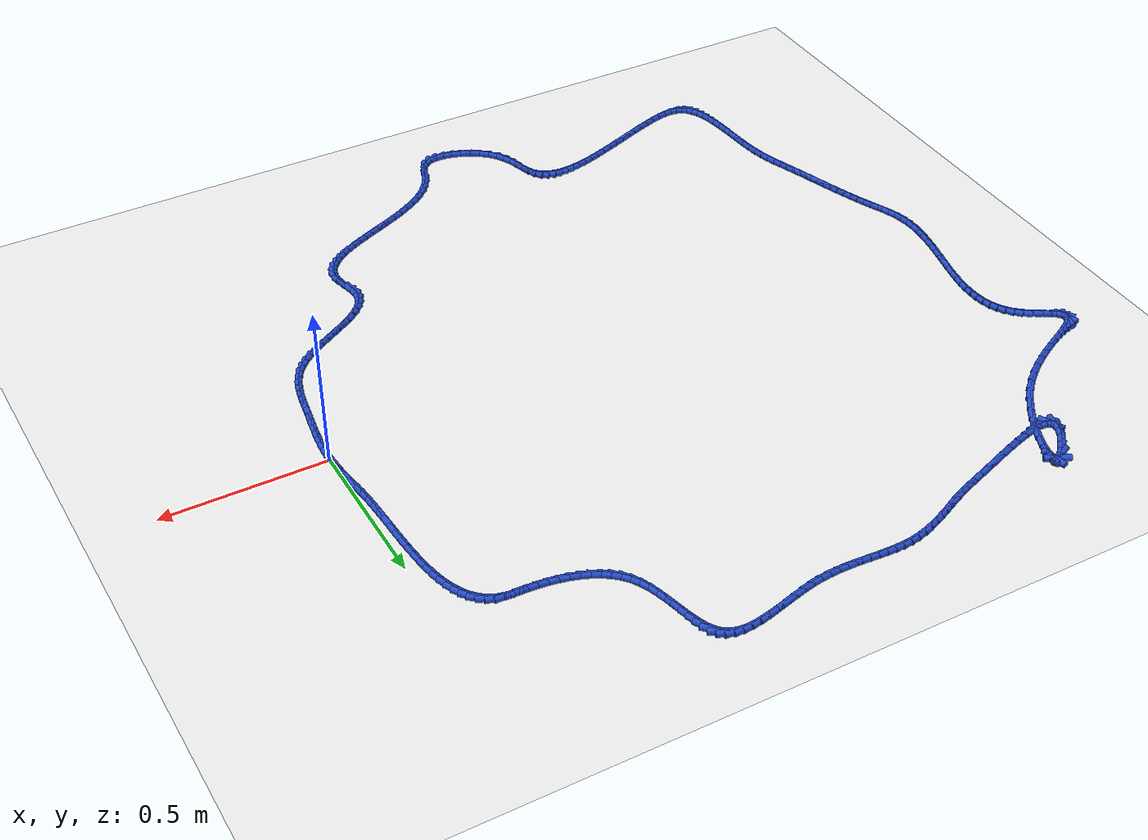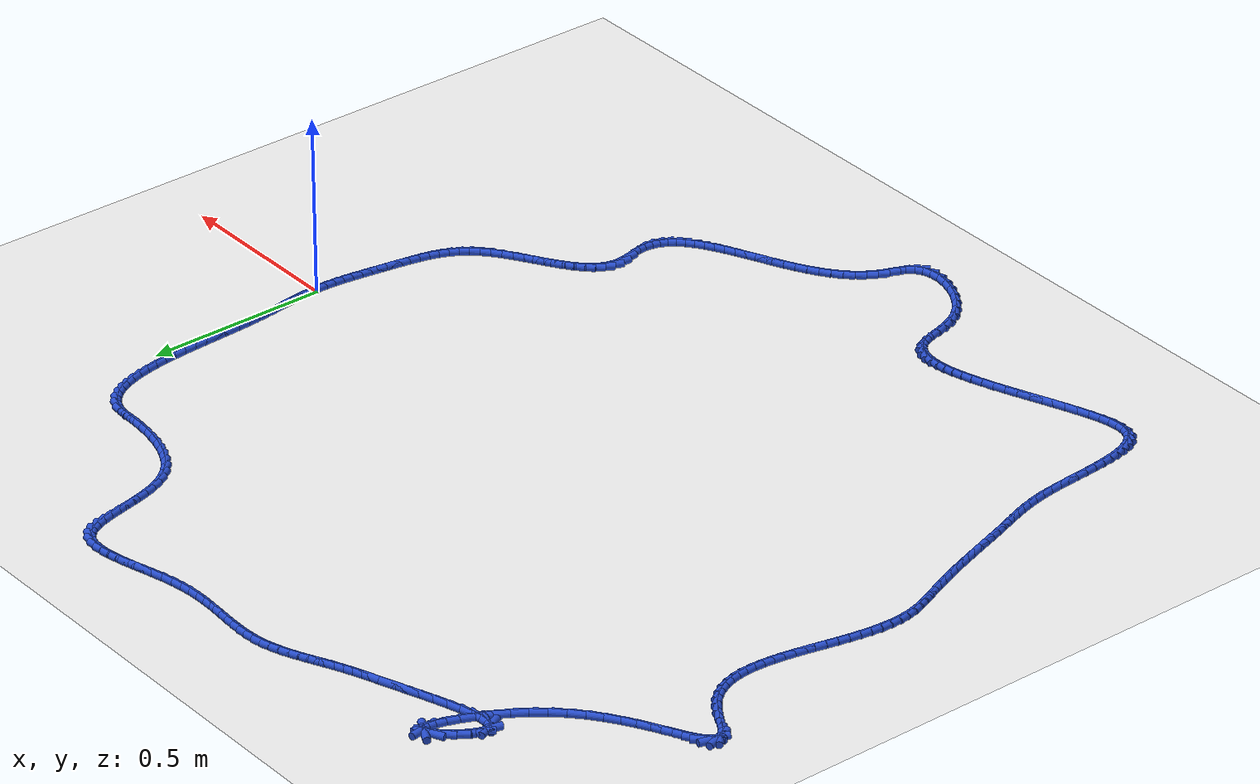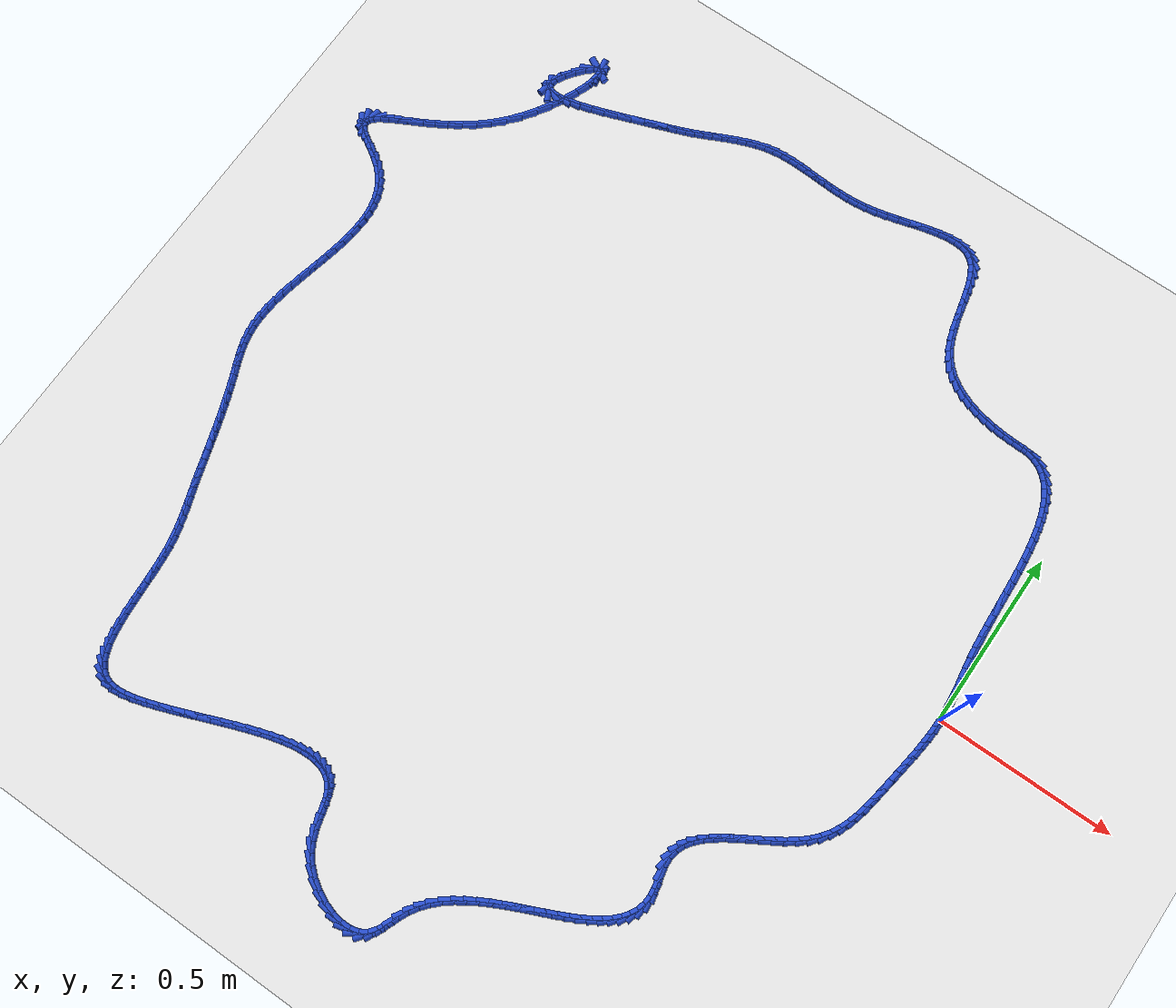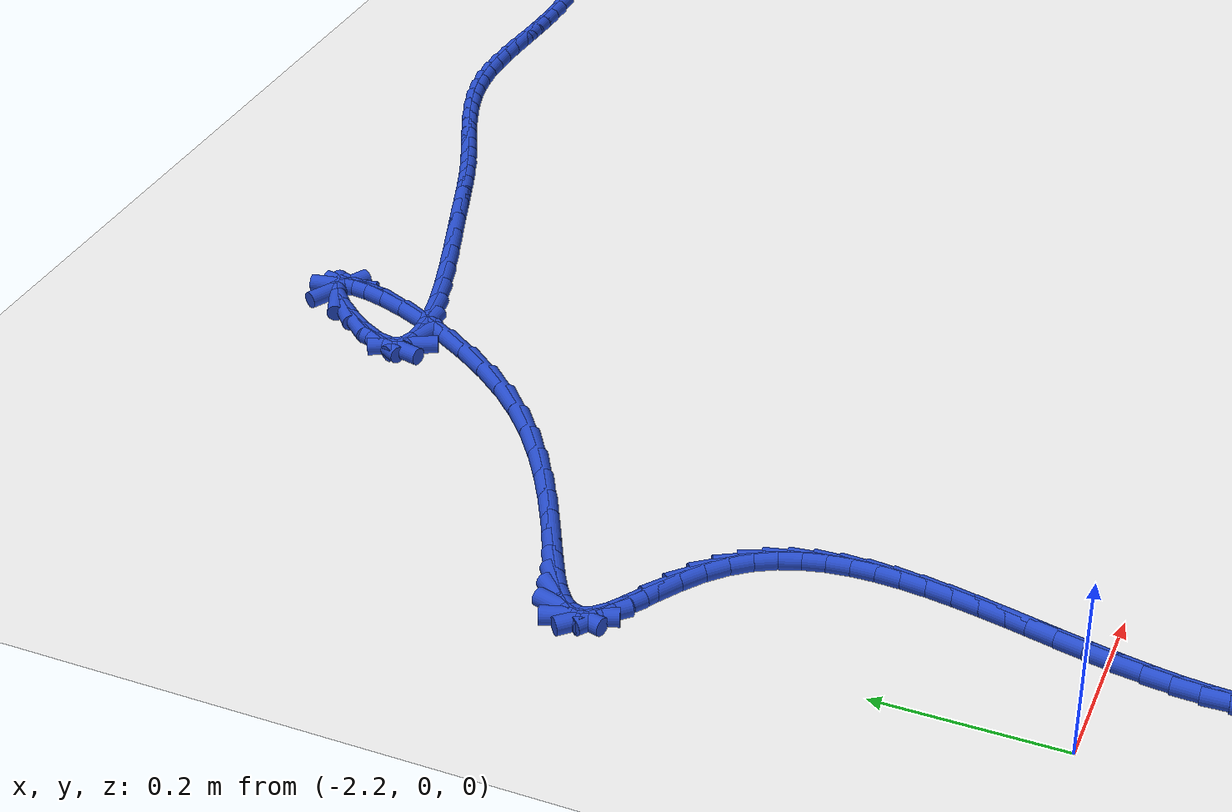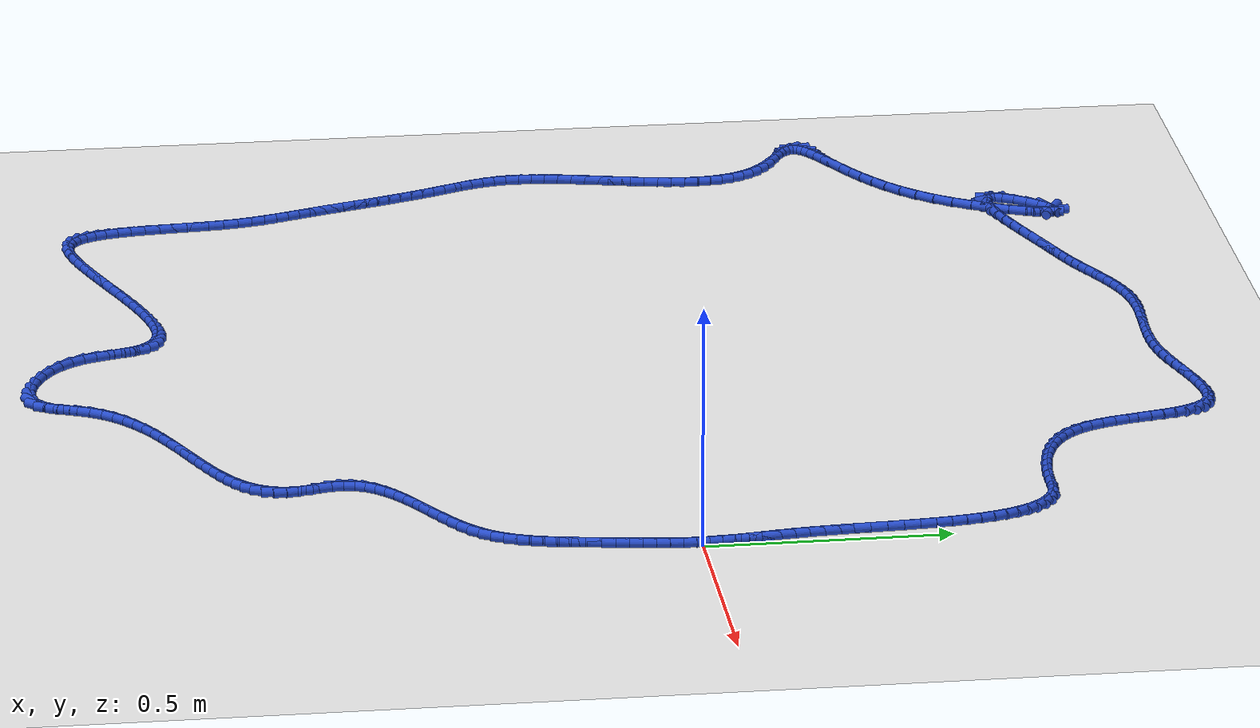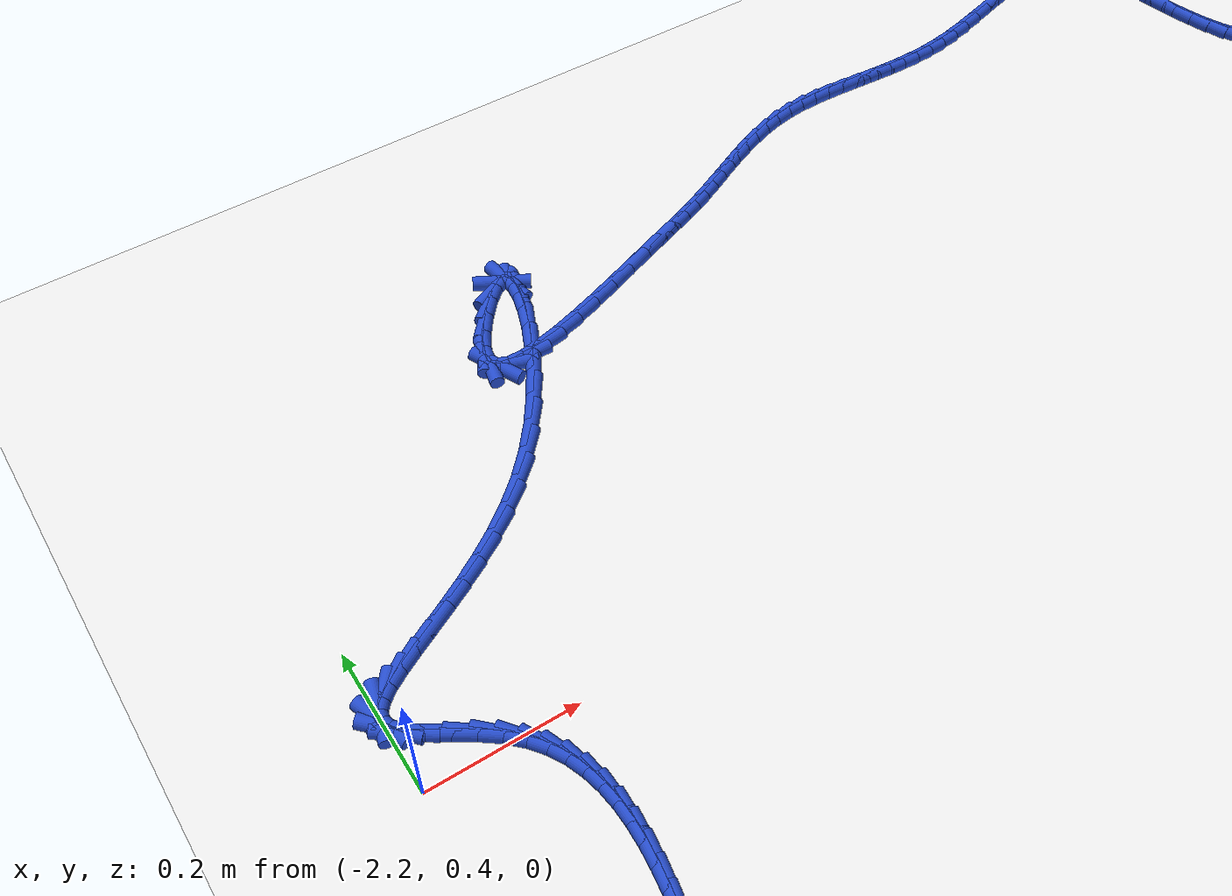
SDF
<sdf version="1.6">
 <world name="default">
  <light name="sun" type="directional">
   <pose>0 0 10 0 -0 0</pose>
   <diffuse>0.8 0.8 0.8 1</diffuse>
   <specular>0.2 0.2 0.2 1</specular>
   <attenuation>
    <range>1000</range>
    <constant>0.9</constant>
    <linear>0.01</linear>
    <quadratic>0.001</quadratic>
   </attenuation>
   <direction>-0.5 0.1 -0.9</direction>
  </light>
  <model name="ground_plane">
   <static>1</static>
   <link name="link">
    <collision name="collision">
     <geometry><plane><normal>0 0 1</normal><size>100 100</size></plane></geometry>
     <surface><friction><ode><mu>100</mu><mu2>50</mu2></ode></friction></surface>
    </collision>
    <visual name="visual">
     <cast_shadows>0</cast_shadows>
     <geometry><plane><normal>0 0 1</normal><size>100 100</size></plane></geometry>
     <material>
      <script><uri>file://media/materials/scripts/gazebo.material</uri><name>Gazebo/WhiteGlow</name></script>
     </material>
    </visual>
   </link>
  </model>
  <gravity>0 0 -9.8</gravity>
  <magnetic_field>6e-06 2.3e-05 -4.2e-05</magnetic_field>
  <atmosphere type="adiabatic"/>
  <physics name="default_physics" default="0" type="ode">
   <max_step_size>0.001</max_step_size>
   <real_time_factor>1</real_time_factor>
   <real_time_update_rate>1000</real_time_update_rate>
  </physics>
  <scene><ambient>0.4 0.4 0.4 1</ambient><background>0.7 0.7 0.7 1</background><shadows>1</shadows></scene>
  <spherical_coordinates>
   <surface_model>EARTH_WGS84</surface_model>
   <latitude_deg>0</latitude_deg>
   <longitude_deg>0</longitude_deg>
   <elevation>0</elevation>
   <heading_deg>0</heading_deg>
  </spherical_coordinates>
  <model name="line">
   <link name="link_0">
    <pose>1.3010426069826053e-17 4.85722573273506e-17 0.01 0 1.57 -1.53374273078391</pose>
    <collision name="collision">
     <geometry><cylinder><radius>0.01</radius><length>0.08</length></cylinder></geometry>
    </collision>
    <visual name="visual">
     <material>
      <script><name>Gazebo/Blue</name><uri>file://media/materials/scripts/gazebo.material</uri></script>
     </material>
     <geometry><cylinder><radius>0.01</radius><length>0.08</length></cylinder></geometry>
    </visual>
   </link>
   <link name="link_1">
    <pose>-0.0009505120971851558 0.02564061661403741 0.01 0 1.57 -1.4929161313203863</pose>
    <collision name="collision">
     <geometry><cylinder><radius>0.01</radius><length>0.08</length></cylinder></geometry>
    </collision>
    <visual name="visual">
     <material>
      <script><name>Gazebo/Blue</name><uri>file://media/materials/scripts/gazebo.material</uri></script>
     </material>
     <geometry><cylinder><radius>0.01</radius><length>0.08</length></cylinder></geometry>
    </visual>
   </link>
   <link name="link_2">
    <pose>-0.0029428397312707944 0.051170829451481735 0.01 0 1.57 -1.4622567356824654</pose>
    <collision name="collision">
     <geometry><cylinder><radius>0.01</radius><length>0.08</length></cylinder></geometry>
    </collision>
    <visual name="visual">
     <material>
      <script><name>Gazebo/Blue</name><uri>file://media/materials/scripts/gazebo.material</uri></script>
     </material>
     <geometry><cylinder><radius>0.01</radius><length>0.08</length></cylinder></geometry>
    </visual>
   </link>
   <link name="link_3">
    <pose>-0.005736424107714438 0.0768076082786417 0.01 0 1.57 -1.4423001634129822</pose>
    <collision name="collision">
     <geometry><cylinder><radius>0.01</radius><length>0.08</length></cylinder></geometry>
    </collision>
    <visual name="visual">
     <material>
      <script><name>Gazebo/Blue</name><uri>file://media/materials/scripts/gazebo.material</uri></script>
     </material>
     <geometry><cylinder><radius>0.01</radius><length>0.08</length></cylinder></geometry>
    </visual>
   </link>
   <link name="link_4">
    <pose>-0.009090706431973608 0.10276792286182596 0.01 0 1.57 -1.4330216142800165</pose>
    <collision name="collision">
     <geometry><cylinder><radius>0.01</radius><length>0.08</length></cylinder></geometry>
    </collision>
    <visual name="visual">
     <material>
      <script><name>Gazebo/Blue</name><uri>file://media/materials/scripts/gazebo.material</uri></script>
     </material>
     <geometry><cylinder><radius>0.01</radius><length>0.08</length></cylinder></geometry>
    </visual>
   </link>
   <link name="link_5">
    <pose>-0.012765127909505838 0.12926874296734314 0.01 0 1.57 -1.4339376347425286</pose>
    <collision name="collision">
     <geometry><cylinder><radius>0.01</radius><length>0.08</length></cylinder></geometry>
    </collision>
    <visual name="visual">
     <material>
      <script><name>Gazebo/Blue</name><uri>file://media/materials/scripts/gazebo.material</uri></script>
     </material>
     <geometry><cylinder><radius>0.01</radius><length>0.08</length></cylinder></geometry>
    </visual>
   </link>
   <link name="link_6">
    <pose>-0.01651912974576864 0.15652703836150186 0.01 0 1.57 -1.4442123722095777</pose>
    <collision name="collision">
     <geometry><cylinder><radius>0.01</radius><length>0.08</length></cylinder></geometry>
    </collision>
    <visual name="visual">
     <material>
      <script><name>Gazebo/Blue</name><uri>file://media/materials/scripts/gazebo.material</uri></script>
     </material>
     <geometry><cylinder><radius>0.01</radius><length>0.08</length></cylinder></geometry>
    </visual>
   </link>
   <link name="link_7">
    <pose>-0.02011215314621956 0.1847597788106109 0.01 0 1.57 -1.4627538627626657</pose>
    <collision name="collision">
     <geometry><cylinder><radius>0.01</radius><length>0.08</length></cylinder></geometry>
    </collision>
    <visual name="visual">
     <material>
      <script><name>Gazebo/Blue</name><uri>file://media/materials/scripts/gazebo.material</uri></script>
     </material>
     <geometry><cylinder><radius>0.01</radius><length>0.08</length></cylinder></geometry>
    </visual>
   </link>
   <link name="link_8">
    <pose>-0.023303639316316117 0.21418393408097874 0.01 0 1.57 -1.4860196869104796</pose>
    <collision name="collision">
     <geometry><cylinder><radius>0.01</radius><length>0.08</length></cylinder></geometry>
    </collision>
    <visual name="visual">
     <material>
      <script><name>Gazebo/Blue</name><uri>file://media/materials/scripts/gazebo.material</uri></script>
     </material>
     <geometry><cylinder><radius>0.01</radius><length>0.08</length></cylinder></geometry>
    </visual>
   </link>
   <link name="link_9">
    <pose>-0.025917331742210545 0.24494037621948112 0.01 0 1.57 -1.503880707562586</pose>
    <collision name="collision">
     <geometry><cylinder><radius>0.01</radius><length>0.08</length></cylinder></geometry>
    </collision>
    <visual name="visual">
     <material>
      <script><name>Gazebo/Blue</name><uri>file://media/materials/scripts/gazebo.material</uri></script>
     </material>
     <geometry><cylinder><radius>0.01</radius><length>0.08</length></cylinder></geometry>
    </visual>
   </link>
   <link name="link_10">
    <pose>-0.028055157753665155 0.27684076412762615 0.01 0 1.57 -1.5147286217173899</pose>
    <collision name="collision">
     <geometry><cylinder><radius>0.01</radius><length>0.08</length></cylinder></geometry>
    </collision>
    <visual name="visual">
     <material>
      <script><name>Gazebo/Blue</name><uri>file://media/materials/scripts/gazebo.material</uri></script>
     </material>
     <geometry><cylinder><radius>0.01</radius><length>0.08</length></cylinder></geometry>
    </visual>
   </link>
   <link name="link_11">
    <pose>-0.02989425498056609 0.30960775003009056 0.01 0 1.57 -1.5193519140829248</pose>
    <collision name="collision">
     <geometry><cylinder><radius>0.01</radius><length>0.08</length></cylinder></geometry>
    </collision>
    <visual name="visual">
     <material>
      <script><name>Gazebo/Blue</name><uri>file://media/materials/scripts/gazebo.material</uri></script>
     </material>
     <geometry><cylinder><radius>0.01</radius><length>0.08</length></cylinder></geometry>
    </visual>
   </link>
   <link name="link_12">
    <pose>-0.03161176229347641 0.34296398468328787 0.01 0 1.57 -1.5181821880731876</pose>
    <collision name="collision">
     <geometry><cylinder><radius>0.01</radius><length>0.08</length></cylinder></geometry>
    </collision>
    <visual name="visual">
     <material>
      <script><name>Gazebo/Blue</name><uri>file://media/materials/scripts/gazebo.material</uri></script>
     </material>
     <geometry><cylinder><radius>0.01</radius><length>0.08</length></cylinder></geometry>
    </visual>
   </link>
   <link name="link_13">
    <pose>-0.03338481856295926 0.37663211884363157 0.01 0 1.57 -1.5113535500675843</pose>
    <collision name="collision">
     <geometry><cylinder><radius>0.01</radius><length>0.08</length></cylinder></geometry>
    </collision>
    <visual name="visual">
     <material>
      <script><name>Gazebo/Blue</name><uri>file://media/materials/scripts/gazebo.material</uri></script>
     </material>
     <geometry><cylinder><radius>0.01</radius><length>0.08</length></cylinder></geometry>
    </visual>
   </link>
   <link name="link_14">
    <pose>-0.03539056265957769 0.410334803267535 0.01 0 1.57 -1.4987283170580756</pose>
    <collision name="collision">
     <geometry><cylinder><radius>0.01</radius><length>0.08</length></cylinder></geometry>
    </collision>
    <visual name="visual">
     <material>
      <script><name>Gazebo/Blue</name><uri>file://media/materials/scripts/gazebo.material</uri></script>
     </material>
     <geometry><cylinder><radius>0.01</radius><length>0.08</length></cylinder></geometry>
    </visual>
   </link>
   <link name="link_15">
    <pose>-0.037806133453894816 0.443794688711412 0.01 0 1.57 -1.479895122322922</pose>
    <collision name="collision">
     <geometry><cylinder><radius>0.01</radius><length>0.08</length></cylinder></geometry>
    </collision>
    <visual name="visual">
     <material>
      <script><name>Gazebo/Blue</name><uri>file://media/materials/scripts/gazebo.material</uri></script>
     </material>
     <geometry><cylinder><radius>0.01</radius><length>0.08</length></cylinder></geometry>
    </visual>
   </link>
   <link name="link_16">
    <pose>-0.04080866981647373 0.47673442593167575 0.01 0 1.57 -1.4541417482149968</pose>
    <collision name="collision">
     <geometry><cylinder><radius>0.01</radius><length>0.08</length></cylinder></geometry>
    </collision>
    <visual name="visual">
     <material>
      <script><name>Gazebo/Blue</name><uri>file://media/materials/scripts/gazebo.material</uri></script>
     </material>
     <geometry><cylinder><radius>0.01</radius><length>0.08</length></cylinder></geometry>
    </visual>
   </link>
   <link name="link_17">
    <pose>-0.04457531061787749 0.5088766656847398 0.01 0 1.57 -1.4204027675378201</pose>
    <collision name="collision">
     <geometry><cylinder><radius>0.01</radius><length>0.08</length></cylinder></geometry>
    </collision>
    <visual name="visual">
     <material>
      <script><name>Gazebo/Blue</name><uri>file://media/materials/scripts/gazebo.material</uri></script>
     </material>
     <geometry><cylinder><radius>0.01</radius><length>0.08</length></cylinder></geometry>
    </visual>
   </link>
   <link name="link_18">
    <pose>-0.04928319472866926 0.5399440587270177 0.01 0 1.57 -1.3771822069479396</pose>
    <collision name="collision">
     <geometry><cylinder><radius>0.01</radius><length>0.08</length></cylinder></geometry>
    </collision>
    <visual name="visual">
     <material>
      <script><name>Gazebo/Blue</name><uri>file://media/materials/scripts/gazebo.material</uri></script>
     </material>
     <geometry><cylinder><radius>0.01</radius><length>0.08</length></cylinder></geometry>
    </visual>
   </link>
   <link name="link_19">
    <pose>-0.05510946101941204 0.5696592558149229 0.01 0 1.57 -1.3224568634582443</pose>
    <collision name="collision">
     <geometry><cylinder><radius>0.01</radius><length>0.08</length></cylinder></geometry>
    </collision>
    <visual name="visual">
     <material>
      <script><name>Gazebo/Blue</name><uri>file://media/materials/scripts/gazebo.material</uri></script>
     </material>
     <geometry><cylinder><radius>0.01</radius><length>0.08</length></cylinder></geometry>
    </visual>
   </link>
   <link name="link_20">
    <pose>-0.06223124836066901 0.597744907704869 0.01 0 1.57 -1.2535839301073037</pose>
    <collision name="collision">
     <geometry><cylinder><radius>0.01</radius><length>0.08</length></cylinder></geometry>
    </collision>
    <visual name="visual">
     <material>
      <script><name>Gazebo/Blue</name><uri>file://media/materials/scripts/gazebo.material</uri></script>
     </material>
     <geometry><cylinder><radius>0.01</radius><length>0.08</length></cylinder></geometry>
    </visual>
   </link>
   <link name="link_21">
    <pose>-0.07082569562300321 0.6239236651532694 0.01 0 1.57 -1.1672826308279138</pose>
    <collision name="collision">
     <geometry><cylinder><radius>0.01</radius><length>0.08</length></cylinder></geometry>
    </collision>
    <visual name="visual">
     <material>
      <script><name>Gazebo/Blue</name><uri>file://media/materials/scripts/gazebo.material</uri></script>
     </material>
     <geometry><cylinder><radius>0.01</radius><length>0.08</length></cylinder></geometry>
    </visual>
   </link>
   <link name="link_22">
    <pose>-0.08106994167697773 0.6479181789165372 0.01 0 1.57 -1.0598574289257567</pose>
    <collision name="collision">
     <geometry><cylinder><radius>0.01</radius><length>0.08</length></cylinder></geometry>
    </collision>
    <visual name="visual">
     <material>
      <script><name>Gazebo/Blue</name><uri>file://media/materials/scripts/gazebo.material</uri></script>
     </material>
     <geometry><cylinder><radius>0.01</radius><length>0.08</length></cylinder></geometry>
    </visual>
   </link>
   <link name="link_23">
    <pose>-0.09314112539315565 0.6694510997510864 0.01 0 1.57 -0.9279842623793714</pose>
    <collision name="collision">
     <geometry><cylinder><radius>0.01</radius><length>0.08</length></cylinder></geometry>
    </collision>
    <visual name="visual">
     <material>
      <script><name>Gazebo/Blue</name><uri>file://media/materials/scripts/gazebo.material</uri></script>
     </material>
     <geometry><cylinder><radius>0.01</radius><length>0.08</length></cylinder></geometry>
    </visual>
   </link>
   <link name="link_24">
    <pose>-0.10721638564210012 0.6882450784133305 0.01 0 1.57 -0.7704530948997941</pose>
    <collision name="collision">
     <geometry><cylinder><radius>0.01</radius><length>0.08</length></cylinder></geometry>
    </collision>
    <visual name="visual">
     <material>
      <script><name>Gazebo/Blue</name><uri>file://media/materials/scripts/gazebo.material</uri></script>
     </material>
     <geometry><cylinder><radius>0.01</radius><length>0.08</length></cylinder></geometry>
    </visual>
   </link>
   <link name="link_25">
    <pose>-0.12347286129437424 0.7040227656596825 0.01 0 1.57 -0.5907556320746858</pose>
    <collision name="collision">
     <geometry><cylinder><radius>0.01</radius><length>0.08</length></cylinder></geometry>
    </collision>
    <visual name="visual">
     <material>
      <script><name>Gazebo/Blue</name><uri>file://media/materials/scripts/gazebo.material</uri></script>
     </material>
     <geometry><cylinder><radius>0.01</radius><length>0.08</length></cylinder></geometry>
    </visual>
   </link>
   <link name="link_26">
    <pose>-0.14208769122054102 0.7165068122465565 0.01 0 1.57 -0.3988299362421815</pose>
    <collision name="collision">
     <geometry><cylinder><radius>0.01</radius><length>0.08</length></cylinder></geometry>
    </collision>
    <visual name="visual">
     <material>
      <script><name>Gazebo/Blue</name><uri>file://media/materials/scripts/gazebo.material</uri></script>
     </material>
     <geometry><cylinder><radius>0.01</radius><length>0.08</length></cylinder></geometry>
    </visual>
   </link>
   <link name="link_27">
    <pose>-0.16323801429116355 0.7254198689303655 0.01 0 1.57 -0.20913837554524453</pose>
    <collision name="collision">
     <geometry><cylinder><radius>0.01</radius><length>0.08</length></cylinder></geometry>
    </collision>
    <visual name="visual">
     <material>
      <script><name>Gazebo/Blue</name><uri>file://media/materials/scripts/gazebo.material</uri></script>
     </material>
     <geometry><cylinder><radius>0.01</radius><length>0.08</length></cylinder></geometry>
    </visual>
   </link>
   <link name="link_28">
    <pose>-0.18710096937680504 0.7304845864675231 0.01 0 1.57 -0.054265456200356436</pose>
    <collision name="collision">
     <geometry><cylinder><radius>0.01</radius><length>0.08</length></cylinder></geometry>
    </collision>
    <visual name="visual">
     <material>
      <script><name>Gazebo/Blue</name><uri>file://media/materials/scripts/gazebo.material</uri></script>
     </material>
     <geometry><cylinder><radius>0.01</radius><length>0.08</length></cylinder></geometry>
    </visual>
   </link>
   <link name="link_29">
    <pose>-0.21364387575481242 0.7319263648896545 0.01 0 1.57 -0.03545689825969489</pose>
    <collision name="collision">
     <geometry><cylinder><radius>0.01</radius><length>0.08</length></cylinder></geometry>
    </collision>
    <visual name="visual">
     <material>
      <script><name>Gazebo/Blue</name><uri>file://media/materials/scripts/gazebo.material</uri></script>
     </material>
     <geometry><cylinder><radius>0.01</radius><length>0.08</length></cylinder></geometry>
    </visual>
   </link>
   <link name="link_30">
    <pose>-0.24157583363481847 0.7329171607199467 0.01 0 1.57 -0.0735758046023805</pose>
    <collision name="collision">
     <geometry><cylinder><radius>0.01</radius><length>0.08</length></cylinder></geometry>
    </collision>
    <visual name="visual">
     <material>
      <script><name>Gazebo/Blue</name><uri>file://media/materials/scripts/gazebo.material</uri></script>
     </material>
     <geometry><cylinder><radius>0.01</radius><length>0.08</length></cylinder></geometry>
    </visual>
   </link>
   <link name="link_31">
    <pose>-0.2700633714432892 0.7350169445927937 0.01 0 1.57 -0.11848462058542499</pose>
    <collision name="collision">
     <geometry><cylinder><radius>0.01</radius><length>0.08</length></cylinder></geometry>
    </collision>
    <visual name="visual">
     <material>
      <script><name>Gazebo/Blue</name><uri>file://media/materials/scripts/gazebo.material</uri></script>
     </material>
     <geometry><cylinder><radius>0.01</radius><length>0.08</length></cylinder></geometry>
    </visual>
   </link>
   <link name="link_32">
    <pose>-0.2987401135043531 0.7384306871947485 0.01 0 1.57 -0.1711285519687538</pose>
    <collision name="collision">
     <geometry><cylinder><radius>0.01</radius><length>0.08</length></cylinder></geometry>
    </collision>
    <visual name="visual">
     <material>
      <script><name>Gazebo/Blue</name><uri>file://media/materials/scripts/gazebo.material</uri></script>
     </material>
     <geometry><cylinder><radius>0.01</radius><length>0.08</length></cylinder></geometry>
    </visual>
   </link>
   <link name="link_33">
    <pose>-0.32724209595021203 0.7433563671300867 0.01 0 1.57 -0.23298757715680704</pose>
    <collision name="collision">
     <geometry><cylinder><radius>0.01</radius><length>0.08</length></cylinder></geometry>
    </collision>
    <visual name="visual">
     <material>
      <script><name>Gazebo/Blue</name><uri>file://media/materials/scripts/gazebo.material</uri></script>
     </material>
     <geometry><cylinder><radius>0.01</radius><length>0.08</length></cylinder></geometry>
    </visual>
   </link>
   <link name="link_34">
    <pose>-0.35520535491306743 0.7499919630030832 0.01 0 1.57 -0.30581323466293264</pose>
    <collision name="collision">
     <geometry><cylinder><radius>0.01</radius><length>0.08</length></cylinder></geometry>
    </collision>
    <visual name="visual">
     <material>
      <script><name>Gazebo/Blue</name><uri>file://media/materials/scripts/gazebo.material</uri></script>
     </material>
     <geometry><cylinder><radius>0.01</radius><length>0.08</length></cylinder></geometry>
    </visual>
   </link>
   <link name="link_35">
    <pose>-0.3822659265251215 0.7585354534180133 0.01 0 1.57 -0.39154602620531154</pose>
    <collision name="collision">
     <geometry><cylinder><radius>0.01</radius><length>0.08</length></cylinder></geometry>
    </collision>
    <visual name="visual">
     <material>
      <script><name>Gazebo/Blue</name><uri>file://media/materials/scripts/gazebo.material</uri></script>
     </material>
     <geometry><cylinder><radius>0.01</radius><length>0.08</length></cylinder></geometry>
    </visual>
   </link>
   <link name="link_36">
    <pose>-0.40805984691857583 0.7691848169791523 0.01 0 1.57 -0.49208527793112045</pose>
    <collision name="collision">
     <geometry><cylinder><radius>0.01</radius><length>0.08</length></cylinder></geometry>
    </collision>
    <visual name="visual">
     <material>
      <script><name>Gazebo/Blue</name><uri>file://media/materials/scripts/gazebo.material</uri></script>
     </material>
     <geometry><cylinder><radius>0.01</radius><length>0.08</length></cylinder></geometry>
    </visual>
   </link>
   <link name="link_37">
    <pose>-0.4322231522256321 0.7821380322907749 0.01 0 1.57 -0.6088142352244349</pose>
    <collision name="collision">
     <geometry><cylinder><radius>0.01</radius><length>0.08</length></cylinder></geometry>
    </collision>
    <visual name="visual">
     <material>
      <script><name>Gazebo/Blue</name><uri>file://media/materials/scripts/gazebo.material</uri></script>
     </material>
     <geometry><cylinder><radius>0.01</radius><length>0.08</length></cylinder></geometry>
    </visual>
   </link>
   <link name="link_38">
    <pose>-0.45439187857849217 0.7975930779571566 0.01 0 1.57 -0.7418243594841966</pose>
    <collision name="collision">
     <geometry><cylinder><radius>0.01</radius><length>0.08</length></cylinder></geometry>
    </collision>
    <visual name="visual">
     <material>
      <script><name>Gazebo/Blue</name><uri>file://media/materials/scripts/gazebo.material</uri></script>
     </material>
     <geometry><cylinder><radius>0.01</radius><length>0.08</length></cylinder></geometry>
    </visual>
   </link>
   <link name="link_39">
    <pose>-0.47420206210935784 0.8157479325825727 0.01 0 1.57 -0.8889833998280542</pose>
    <collision name="collision">
     <geometry><cylinder><radius>0.01</radius><length>0.08</length></cylinder></geometry>
    </collision>
    <visual name="visual">
     <material>
      <script><name>Gazebo/Blue</name><uri>file://media/materials/scripts/gazebo.material</uri></script>
     </material>
     <geometry><cylinder><radius>0.01</radius><length>0.08</length></cylinder></geometry>
    </visual>
   </link>
   <link name="link_40">
    <pose>-0.4912897389504308 0.8368005747712982 0.01 0 1.57 -1.0404978819189734</pose>
    <collision name="collision">
     <geometry><cylinder><radius>0.01</radius><length>0.08</length></cylinder></geometry>
    </collision>
    <visual name="visual">
     <material>
      <script><name>Gazebo/Blue</name><uri>file://media/materials/scripts/gazebo.material</uri></script>
     </material>
     <geometry><cylinder><radius>0.01</radius><length>0.08</length></cylinder></geometry>
    </visual>
   </link>
   <link name="link_41">
    <pose>-0.5053901916258616 0.8608497308193352 0.01 0 1.57 -1.162971881866138</pose>
    <collision name="collision">
     <geometry><cylinder><radius>0.01</radius><length>0.08</length></cylinder></geometry>
    </collision>
    <visual name="visual">
     <material>
      <script><name>Gazebo/Blue</name><uri>file://media/materials/scripts/gazebo.material</uri></script>
     </material>
     <geometry><cylinder><radius>0.01</radius><length>0.08</length></cylinder></geometry>
    </visual>
   </link>
   <link name="link_42">
    <pose>-0.5168526009541179 0.8873801921323666 0.01 0 1.57 -1.249450072627195</pose>
    <collision name="collision">
     <geometry><cylinder><radius>0.01</radius><length>0.08</length></cylinder></geometry>
    </collision>
    <visual name="visual">
     <material>
      <script><name>Gazebo/Blue</name><uri>file://media/materials/scripts/gazebo.material</uri></script>
     </material>
     <geometry><cylinder><radius>0.01</radius><length>0.08</length></cylinder></geometry>
    </visual>
   </link>
   <link name="link_43">
    <pose>-0.526260602964229 0.9156422809290542 0.01 0 1.57 -1.3057484327358289</pose>
    <collision name="collision">
     <geometry><cylinder><radius>0.01</radius><length>0.08</length></cylinder></geometry>
    </collision>
    <visual name="visual">
     <material>
      <script><name>Gazebo/Blue</name><uri>file://media/materials/scripts/gazebo.material</uri></script>
     </material>
     <geometry><cylinder><radius>0.01</radius><length>0.08</length></cylinder></geometry>
    </visual>
   </link>
   <link name="link_44">
    <pose>-0.5341983016053953 0.9448858514799972 0.01 0 1.57 -1.3359725627695545</pose>
    <collision name="collision">
     <geometry><cylinder><radius>0.01</radius><length>0.08</length></cylinder></geometry>
    </collision>
    <visual name="visual">
     <material>
      <script><name>Gazebo/Blue</name><uri>file://media/materials/scripts/gazebo.material</uri></script>
     </material>
     <geometry><cylinder><radius>0.01</radius><length>0.08</length></cylinder></geometry>
    </visual>
   </link>
   <link name="link_45">
    <pose>-0.5412498008268156 0.9743607580557938 0.01 0 1.57 -1.3417942864793853</pose>
    <collision name="collision">
     <geometry><cylinder><radius>0.01</radius><length>0.08</length></cylinder></geometry>
    </collision>
    <visual name="visual">
     <material>
      <script><name>Gazebo/Blue</name><uri>file://media/materials/scripts/gazebo.material</uri></script>
     </material>
     <geometry><cylinder><radius>0.01</radius><length>0.08</length></cylinder></geometry>
    </visual>
   </link>
   <link name="link_46">
    <pose>-0.54799920457769 1.0033168549270424 0.01 0 1.57 -1.3220945736978469</pose>
    <collision name="collision">
     <geometry><cylinder><radius>0.01</radius><length>0.08</length></cylinder></geometry>
    </collision>
    <visual name="visual">
     <material>
      <script><name>Gazebo/Blue</name><uri>file://media/materials/scripts/gazebo.material</uri></script>
     </material>
     <geometry><cylinder><radius>0.01</radius><length>0.08</length></cylinder></geometry>
    </visual>
   </link>
   <link name="link_47">
    <pose>-0.555030616807218 1.031003996364342 0.01 0 1.57 -1.2723092781854561</pose>
    <collision name="collision">
     <geometry><cylinder><radius>0.01</radius><length>0.08</length></cylinder></geometry>
    </collision>
    <visual name="visual">
     <material>
      <script><name>Gazebo/Blue</name><uri>file://media/materials/scripts/gazebo.material</uri></script>
     </material>
     <geometry><cylinder><radius>0.01</radius><length>0.08</length></cylinder></geometry>
    </visual>
   </link>
   <link name="link_48">
    <pose>-0.5629281414645995 1.0566720366382916 0.01 0 1.57 -1.1832240540384102</pose>
    <collision name="collision">
     <geometry><cylinder><radius>0.01</radius><length>0.08</length></cylinder></geometry>
    </collision>
    <visual name="visual">
     <material>
      <script><name>Gazebo/Blue</name><uri>file://media/materials/scripts/gazebo.material</uri></script>
     </material>
     <geometry><cylinder><radius>0.01</radius><length>0.08</length></cylinder></geometry>
    </visual>
   </link>
   <link name="link_49">
    <pose>-0.5722758824990334 1.0795708300194886 0.01 0 1.57 -1.0397467110572345</pose>
    <collision name="collision">
     <geometry><cylinder><radius>0.01</radius><length>0.08</length></cylinder></geometry>
    </collision>
    <visual name="visual">
     <material>
      <script><name>Gazebo/Blue</name><uri>file://media/materials/scripts/gazebo.material</uri></script>
     </material>
     <geometry><cylinder><radius>0.01</radius><length>0.08</length></cylinder></geometry>
    </visual>
   </link>
   <link name="link_50">
    <pose>-0.5836579438597201 1.098950230778533 0.01 0 1.57 -0.8234890917243034</pose>
    <collision name="collision">
     <geometry><cylinder><radius>0.01</radius><length>0.08</length></cylinder></geometry>
    </collision>
    <visual name="visual">
     <material>
      <script><name>Gazebo/Blue</name><uri>file://media/materials/scripts/gazebo.material</uri></script>
     </material>
     <geometry><cylinder><radius>0.01</radius><length>0.08</length></cylinder></geometry>
    </visual>
   </link>
   <link name="link_51">
    <pose>-0.5976584294958587 1.1140600931860223 0.01 0 1.57 -0.5417472938021559</pose>
    <collision name="collision">
     <geometry><cylinder><radius>0.01</radius><length>0.08</length></cylinder></geometry>
    </collision>
    <visual name="visual">
     <material>
      <script><name>Gazebo/Blue</name><uri>file://media/materials/scripts/gazebo.material</uri></script>
     </material>
     <geometry><cylinder><radius>0.01</radius><length>0.08</length></cylinder></geometry>
    </visual>
   </link>
   <link name="link_52">
    <pose>-0.6147346970407093 1.1243367146275443 0.01 0 1.57 -0.2817296846337053</pose>
    <collision name="collision">
     <geometry><cylinder><radius>0.01</radius><length>0.08</length></cylinder></geometry>
    </collision>
    <visual name="visual">
     <material>
      <script><name>Gazebo/Blue</name><uri>file://media/materials/scripts/gazebo.material</uri></script>
     </material>
     <geometry><cylinder><radius>0.01</radius><length>0.08</length></cylinder></geometry>
    </visual>
   </link>
   <link name="link_53">
    <pose>-0.6347276265189858 1.1301232275694975 0.01 0 1.57 -0.08466259850490172</pose>
    <collision name="collision">
     <geometry><cylinder><radius>0.01</radius><length>0.08</length></cylinder></geometry>
    </collision>
    <visual name="visual">
     <material>
      <script><name>Gazebo/Blue</name><uri>file://media/materials/scripts/gazebo.material</uri></script>
     </material>
     <geometry><cylinder><radius>0.01</radius><length>0.08</length></cylinder></geometry>
    </visual>
   </link>
   <link name="link_54">
    <pose>-0.6572909394967803 1.1320380735139974 0.01 0 1.57 0.053939501060476854</pose>
    <collision name="collision">
     <geometry><cylinder><radius>0.01</radius><length>0.08</length></cylinder></geometry>
    </collision>
    <visual name="visual">
     <material>
      <script><name>Gazebo/Blue</name><uri>file://media/materials/scripts/gazebo.material</uri></script>
     </material>
     <geometry><cylinder><radius>0.01</radius><length>0.08</length></cylinder></geometry>
    </visual>
   </link>
   <link name="link_55">
    <pose>-0.682078314912072 1.1306997566688721 0.01 0 1.57 0.14790715090181028</pose>
    <collision name="collision">
     <geometry><cylinder><radius>0.01</radius><length>0.08</length></cylinder></geometry>
    </collision>
    <visual name="visual">
     <material>
      <script><name>Gazebo/Blue</name><uri>file://media/materials/scripts/gazebo.material</uri></script>
     </material>
     <geometry><cylinder><radius>0.01</radius><length>0.08</length></cylinder></geometry>
    </visual>
   </link>
   <link name="link_56">
    <pose>-0.7087434317028406 1.1267267812419504 0.01 0 1.57 0.2092960002546825</pose>
    <collision name="collision">
     <geometry><cylinder><radius>0.01</radius><length>0.08</length></cylinder></geometry>
    </collision>
    <visual name="visual">
     <material>
      <script><name>Gazebo/Blue</name><uri>file://media/materials/scripts/gazebo.material</uri></script>
     </material>
     <geometry><cylinder><radius>0.01</radius><length>0.08</length></cylinder></geometry>
    </visual>
   </link>
   <link name="link_57">
    <pose>-0.736939968807065 1.1207376514410599 0.01 0 1.57 0.24630344905452578</pose>
    <collision name="collision">
     <geometry><cylinder><radius>0.01</radius><length>0.08</length></cylinder></geometry>
    </collision>
    <visual name="visual">
     <material>
      <script><name>Gazebo/Blue</name><uri>file://media/materials/scripts/gazebo.material</uri></script>
     </material>
     <geometry><cylinder><radius>0.01</radius><length>0.08</length></cylinder></geometry>
    </visual>
   </link>
   <link name="link_58">
    <pose>-0.7663216051627246 1.1133508714740288 0.01 0 1.57 0.26390964342603934</pose>
    <collision name="collision">
     <geometry><cylinder><radius>0.01</radius><length>0.08</length></cylinder></geometry>
    </collision>
    <visual name="visual">
     <material>
      <script><name>Gazebo/Blue</name><uri>file://media/materials/scripts/gazebo.material</uri></script>
     </material>
     <geometry><cylinder><radius>0.01</radius><length>0.08</length></cylinder></geometry>
    </visual>
   </link>
   <link name="link_59">
    <pose>-0.7965420197077984 1.105184945548686 0.01 0 1.57 0.26474615580008765</pose>
    <collision name="collision">
     <geometry><cylinder><radius>0.01</radius><length>0.08</length></cylinder></geometry>
    </collision>
    <visual name="visual">
     <material>
      <script><name>Gazebo/Blue</name><uri>file://media/materials/scripts/gazebo.material</uri></script>
     </material>
     <geometry><cylinder><radius>0.01</radius><length>0.08</length></cylinder></geometry>
    </visual>
   </link>
   <link name="link_60">
    <pose>-0.8272548913802661 1.0968583778728587 0.01 0 1.57 0.24966858246289933</pose>
    <collision name="collision">
     <geometry><cylinder><radius>0.01</radius><length>0.08</length></cylinder></geometry>
    </collision>
    <visual name="visual">
     <material>
      <script><name>Gazebo/Blue</name><uri>file://media/materials/scripts/gazebo.material</uri></script>
     </material>
     <geometry><cylinder><radius>0.01</radius><length>0.08</length></cylinder></geometry>
    </visual>
   </link>
   <link name="link_61">
    <pose>-0.8581138991181072 1.088989672654376 0.01 0 1.57 0.21802442290079138</pose>
    <collision name="collision">
     <geometry><cylinder><radius>0.01</radius><length>0.08</length></cylinder></geometry>
    </collision>
    <visual name="visual">
     <material>
      <script><name>Gazebo/Blue</name><uri>file://media/materials/scripts/gazebo.material</uri></script>
     </material>
     <geometry><cylinder><radius>0.01</radius><length>0.08</length></cylinder></geometry>
    </visual>
   </link>
   <link name="link_62">
    <pose>-0.8887727218593002 1.0821973341010658 0.01 0 1.57 0.1677948711607212</pose>
    <collision name="collision">
     <geometry><cylinder><radius>0.01</radius><length>0.08</length></cylinder></geometry>
    </collision>
    <visual name="visual">
     <material>
      <script><name>Gazebo/Blue</name><uri>file://media/materials/scripts/gazebo.material</uri></script>
     </material>
     <geometry><cylinder><radius>0.01</radius><length>0.08</length></cylinder></geometry>
    </visual>
   </link>
   <link name="link_63">
    <pose>-0.9188865022994168 1.0770964339439755 0.01 0 1.57 0.10590770142750167</pose>
    <collision name="collision">
     <geometry><cylinder><radius>0.01</radius><length>0.08</length></cylinder></geometry>
    </collision>
    <visual name="visual">
     <material>
      <script><name>Gazebo/Blue</name><uri>file://media/materials/scripts/gazebo.material</uri></script>
     </material>
     <geometry><cylinder><radius>0.01</radius><length>0.08</length></cylinder></geometry>
    </visual>
   </link>
   <link name="link_64">
    <pose>-0.9482498712301497 1.0739749476422635 0.01 0 1.57 0.05043483621390203</pose>
    <collision name="collision">
     <geometry><cylinder><radius>0.01</radius><length>0.08</length></cylinder></geometry>
    </collision>
    <visual name="visual">
     <material>
      <script><name>Gazebo/Blue</name><uri>file://media/materials/scripts/gazebo.material</uri></script>
     </material>
     <geometry><cylinder><radius>0.01</radius><length>0.08</length></cylinder></geometry>
    </visual>
   </link>
   <link name="link_65">
    <pose>-0.9769101730900047 1.0725282431564873 0.01 0 1.57 0.0049602346354941425</pose>
    <collision name="collision">
     <geometry><cylinder><radius>0.01</radius><length>0.08</length></cylinder></geometry>
    </collision>
    <visual name="visual">
     <material>
      <script><name>Gazebo/Blue</name><uri>file://media/materials/scripts/gazebo.material</uri></script>
     </material>
     <geometry><cylinder><radius>0.01</radius><length>0.08</length></cylinder></geometry>
    </visual>
   </link>
   <link name="link_66">
    <pose>-1.0049413998765668 1.072389200554172 0.01 0 1.57 -0.029162466634927737</pose>
    <collision name="collision">
     <geometry><cylinder><radius>0.01</radius><length>0.08</length></cylinder></geometry>
    </collision>
    <visual name="visual">
     <material>
      <script><name>Gazebo/Blue</name><uri>file://media/materials/scripts/gazebo.material</uri></script>
     </material>
     <geometry><cylinder><radius>0.01</radius><length>0.08</length></cylinder></geometry>
    </visual>
   </link>
   <link name="link_67">
    <pose>-1.0324175435874205 1.0731906999028422 0.01 0 1.57 -0.05088837338573158</pose>
    <collision name="collision">
     <geometry><cylinder><radius>0.01</radius><length>0.08</length></cylinder></geometry>
    </collision>
    <visual name="visual">
     <material>
      <script><name>Gazebo/Blue</name><uri>file://media/materials/scripts/gazebo.material</uri></script>
     </material>
     <geometry><cylinder><radius>0.01</radius><length>0.08</length></cylinder></geometry>
    </visual>
   </link>
   <link name="link_68">
    <pose>-1.0594125962201517 1.0745656212700239 0.01 0 1.57 -0.05940145835717837</pose>
    <collision name="collision">
     <geometry><cylinder><radius>0.01</radius><length>0.08</length></cylinder></geometry>
    </collision>
    <visual name="visual">
     <material>
      <script><name>Gazebo/Blue</name><uri>file://media/materials/scripts/gazebo.material</uri></script>
     </material>
     <geometry><cylinder><radius>0.01</radius><length>0.08</length></cylinder></geometry>
    </visual>
   </link>
   <link name="link_69">
    <pose>-1.086000549772344 1.0761468447232412 0.01 0 1.57 -0.05404801161643357</pose>
    <collision name="collision">
     <geometry><cylinder><radius>0.01</radius><length>0.08</length></cylinder></geometry>
    </collision>
    <visual name="visual">
     <material>
      <script><name>Gazebo/Blue</name><uri>file://media/materials/scripts/gazebo.material</uri></script>
     </material>
     <geometry><cylinder><radius>0.01</radius><length>0.08</length></cylinder></geometry>
    </visual>
   </link>
   <link name="link_70">
    <pose>-1.112255396241583 1.0775672503300204 0.01 0 1.57 -0.03431784356362337</pose>
    <collision name="collision">
     <geometry><cylinder><radius>0.01</radius><length>0.08</length></cylinder></geometry>
    </collision>
    <visual name="visual">
     <material>
      <script><name>Gazebo/Blue</name><uri>file://media/materials/scripts/gazebo.material</uri></script>
     </material>
     <geometry><cylinder><radius>0.01</radius><length>0.08</length></cylinder></geometry>
    </visual>
   </link>
   <link name="link_71">
    <pose>-1.1382511276254532 1.0784597181578854 0.01 0 1.57 0.0001003418239902149</pose>
    <collision name="collision">
     <geometry><cylinder><radius>0.01</radius><length>0.08</length></cylinder></geometry>
    </collision>
    <visual name="visual">
     <material>
      <script><name>Gazebo/Blue</name><uri>file://media/materials/scripts/gazebo.material</uri></script>
     </material>
     <geometry><cylinder><radius>0.01</radius><length>0.08</length></cylinder></geometry>
    </visual>
   </link>
   <link name="link_72">
    <pose>-1.16406173592154 1.078457128274362 0.01 0 1.57 0.04917407123176072</pose>
    <collision name="collision">
     <geometry><cylinder><radius>0.01</radius><length>0.08</length></cylinder></geometry>
    </collision>
    <visual name="visual">
     <material>
      <script><name>Gazebo/Blue</name><uri>file://media/materials/scripts/gazebo.material</uri></script>
     </material>
     <geometry><cylinder><radius>0.01</radius><length>0.08</length></cylinder></geometry>
    </visual>
   </link>
   <link name="link_73">
    <pose>-1.1897612131274282 1.0771923607469758 0.01 0 1.57 0.11230032179949456</pose>
    <collision name="collision">
     <geometry><cylinder><radius>0.01</radius><length>0.08</length></cylinder></geometry>
    </collision>
    <visual name="visual">
     <material>
      <script><name>Gazebo/Blue</name><uri>file://media/materials/scripts/gazebo.material</uri></script>
     </material>
     <geometry><cylinder><radius>0.01</radius><length>0.08</length></cylinder></geometry>
    </visual>
   </link>
   <link name="link_74">
    <pose>-1.215423551240702 1.0742982956432507 0.01 0 1.57 0.18803626252625102</pose>
    <collision name="collision">
     <geometry><cylinder><radius>0.01</radius><length>0.08</length></cylinder></geometry>
    </collision>
    <visual name="visual">
     <material>
      <script><name>Gazebo/Blue</name><uri>file://media/materials/scripts/gazebo.material</uri></script>
     </material>
     <geometry><cylinder><radius>0.01</radius><length>0.08</length></cylinder></geometry>
    </visual>
   </link>
   <link name="link_75">
    <pose>-1.2411226610532975 1.0694081602272765 0.01 0 1.57 0.26725021763107903</pose>
    <collision name="collision">
     <geometry><cylinder><radius>0.01</radius><length>0.08</length></cylinder></geometry>
    </collision>
    <visual name="visual">
     <material>
      <script><name>Gazebo/Blue</name><uri>file://media/materials/scripts/gazebo.material</uri></script>
     </material>
     <geometry><cylinder><radius>0.01</radius><length>0.08</length></cylinder></geometry>
    </visual>
   </link>
   <link name="link_76">
    <pose>-1.2668859089203777 1.062354183540421 0.01 0 1.57 0.3314071847718676</pose>
    <collision name="collision">
     <geometry><cylinder><radius>0.01</radius><length>0.08</length></cylinder></geometry>
    </collision>
    <visual name="visual">
     <material>
      <script><name>Gazebo/Blue</name><uri>file://media/materials/scripts/gazebo.material</uri></script>
     </material>
     <geometry><cylinder><radius>0.01</radius><length>0.08</length></cylinder></geometry>
    </visual>
   </link>
   <link name="link_77">
    <pose>-1.2926162730056359 1.0535004191103163 0.01 0 1.57 0.3794829756522754</pose>
    <collision name="collision">
     <geometry><cylinder><radius>0.01</radius><length>0.08</length></cylinder></geometry>
    </collision>
    <visual name="visual">
     <material>
      <script><name>Gazebo/Blue</name><uri>file://media/materials/scripts/gazebo.material</uri></script>
     </material>
     <geometry><cylinder><radius>0.01</radius><length>0.08</length></cylinder></geometry>
    </visual>
   </link>
   <link name="link_78">
    <pose>-1.3181961742660286 1.0432988132603842 0.01 0 1.57 0.4131915084848422</pose>
    <collision name="collision">
     <geometry><cylinder><radius>0.01</radius><length>0.08</length></cylinder></geometry>
    </collision>
    <visual name="visual">
     <material>
      <script><name>Gazebo/Blue</name><uri>file://media/materials/scripts/gazebo.material</uri></script>
     </material>
     <geometry><cylinder><radius>0.01</radius><length>0.08</length></cylinder></geometry>
    </visual>
   </link>
   <link name="link_79">
    <pose>-1.3435080336585126 1.0322013123140459 0.01 0 1.57 0.4336318480567967</pose>
    <collision name="collision">
     <geometry><cylinder><radius>0.01</radius><length>0.08</length></cylinder></geometry>
    </collision>
    <visual name="visual">
     <material>
      <script><name>Gazebo/Blue</name><uri>file://media/materials/scripts/gazebo.material</uri></script>
     </material>
     <geometry><cylinder><radius>0.01</radius><length>0.08</length></cylinder></geometry>
    </visual>
   </link>
   <link name="link_80">
    <pose>-1.368434272140044 1.0206598625947232 0.01 0 1.57 0.4411912195894931</pose>
    <collision name="collision">
     <geometry><cylinder><radius>0.01</radius><length>0.08</length></cylinder></geometry>
    </collision>
    <visual name="visual">
     <material>
      <script><name>Gazebo/Blue</name><uri>file://media/materials/scripts/gazebo.material</uri></script>
     </material>
     <geometry><cylinder><radius>0.01</radius><length>0.08</length></cylinder></geometry>
    </visual>
   </link>
   <link name="link_81">
    <pose>-1.3928573106675803 1.0091264104258382 0.01 0 1.57 0.4354461820691759</pose>
    <collision name="collision">
     <geometry><cylinder><radius>0.01</radius><length>0.08</length></cylinder></geometry>
    </collision>
    <visual name="visual">
     <material>
      <script><name>Gazebo/Blue</name><uri>file://media/materials/scripts/gazebo.material</uri></script>
     </material>
     <geometry><cylinder><radius>0.01</radius><length>0.08</length></cylinder></geometry>
    </visual>
   </link>
   <link name="link_82">
    <pose>-1.416659570198078 0.998052902130812 0.01 0 1.57 0.4153448313387863</pose>
    <collision name="collision">
     <geometry><cylinder><radius>0.01</radius><length>0.08</length></cylinder></geometry>
    </collision>
    <visual name="visual">
     <material>
      <script><name>Gazebo/Blue</name><uri>file://media/materials/scripts/gazebo.material</uri></script>
     </material>
     <geometry><cylinder><radius>0.01</radius><length>0.08</length></cylinder></geometry>
    </visual>
   </link>
   <link name="link_83">
    <pose>-1.4397403562009665 0.9878742627093712 0.01 0 1.57 0.3884635753428459</pose>
    <collision name="collision">
     <geometry><cylinder><radius>0.01</radius><length>0.08</length></cylinder></geometry>
    </collision>
    <visual name="visual">
     <material>
      <script><name>Gazebo/Blue</name><uri>file://media/materials/scripts/gazebo.material</uri></script>
     </material>
     <geometry><cylinder><radius>0.01</radius><length>0.08</length></cylinder></geometry>
    </visual>
   </link>
   <link name="link_84">
    <pose>-1.462434341952853 0.9785865216714222 0.01 0 1.57 0.36646536756991704</pose>
    <collision name="collision">
     <geometry><cylinder><radius>0.01</radius><length>0.08</length></cylinder></geometry>
    </collision>
    <visual name="visual">
     <material>
      <script><name>Gazebo/Blue</name><uri>file://media/materials/scripts/gazebo.material</uri></script>
     </material>
     <geometry><cylinder><radius>0.01</radius><length>0.08</length></cylinder></geometry>
    </visual>
   </link>
   <link name="link_85">
    <pose>-1.4855394154863828 0.9697187404509291 0.01 0 1.57 0.35209717756006437</pose>
    <collision name="collision">
     <geometry><cylinder><radius>0.01</radius><length>0.08</length></cylinder></geometry>
    </collision>
    <visual name="visual">
     <material>
      <script><name>Gazebo/Blue</name><uri>file://media/materials/scripts/gazebo.material</uri></script>
     </material>
     <geometry><cylinder><radius>0.01</radius><length>0.08</length></cylinder></geometry>
    </visual>
   </link>
   <link name="link_86">
    <pose>-1.5098759254484428 0.9607773378745577 0.01 0 1.57 0.34585140345293613</pose>
    <collision name="collision">
     <geometry><cylinder><radius>0.01</radius><length>0.08</length></cylinder></geometry>
    </collision>
    <visual name="visual">
     <material>
      <script><name>Gazebo/Blue</name><uri>file://media/materials/scripts/gazebo.material</uri></script>
     </material>
     <geometry><cylinder><radius>0.01</radius><length>0.08</length></cylinder></geometry>
    </visual>
   </link>
   <link name="link_87">
    <pose>-1.536264220485918 0.9512687327689737 0.01 0 1.57 0.3466332760400018</pose>
    <collision name="collision">
     <geometry><cylinder><radius>0.01</radius><length>0.08</length></cylinder></geometry>
    </collision>
    <visual name="visual">
     <material>
      <script><name>Gazebo/Blue</name><uri>file://media/materials/scripts/gazebo.material</uri></script>
     </material>
     <geometry><cylinder><radius>0.01</radius><length>0.08</length></cylinder></geometry>
    </visual>
   </link>
   <link name="link_88">
    <pose>-1.565524649245695 0.9406993439608429 0.01 0 1.57 0.35126762538853873</pose>
    <collision name="collision">
     <geometry><cylinder><radius>0.01</radius><length>0.08</length></cylinder></geometry>
    </collision>
    <visual name="visual">
     <material>
      <script><name>Gazebo/Blue</name><uri>file://media/materials/scripts/gazebo.material</uri></script>
     </material>
     <geometry><cylinder><radius>0.01</radius><length>0.08</length></cylinder></geometry>
    </visual>
   </link>
   <link name="link_89">
    <pose>-1.5982908010272654 0.9286916734815941 0.01 0 1.57 0.34972330098774573</pose>
    <collision name="collision">
     <geometry><cylinder><radius>0.01</radius><length>0.08</length></cylinder></geometry>
    </collision>
    <visual name="visual">
     <material>
      <script><name>Gazebo/Blue</name><uri>file://media/materials/scripts/gazebo.material</uri></script>
     </material>
     <geometry><cylinder><radius>0.01</radius><length>0.08</length></cylinder></geometry>
    </visual>
   </link>
   <link name="link_90">
    <pose>-1.6337811424553943 0.9157478150806083 0.01 0 1.57 0.3391039021439201</pose>
    <collision name="collision">
     <geometry><cylinder><radius>0.01</radius><length>0.08</length></cylinder></geometry>
    </collision>
    <visual name="visual">
     <material>
      <script><name>Gazebo/Blue</name><uri>file://media/materials/scripts/gazebo.material</uri></script>
     </material>
     <geometry><cylinder><radius>0.01</radius><length>0.08</length></cylinder></geometry>
    </visual>
   </link>
   <link name="link_91">
    <pose>-1.6705659779128599 0.9027727379258548 0.01 0 1.57 0.3188943592542334</pose>
    <collision name="collision">
     <geometry><cylinder><radius>0.01</radius><length>0.08</length></cylinder></geometry>
    </collision>
    <visual name="visual">
     <material>
      <script><name>Gazebo/Blue</name><uri>file://media/materials/scripts/gazebo.material</uri></script>
     </material>
     <geometry><cylinder><radius>0.01</radius><length>0.08</length></cylinder></geometry>
    </visual>
   </link>
   <link name="link_92">
    <pose>-1.7072122444325066 0.8906735042145273 0.01 0 1.57 0.28605823978131106</pose>
    <collision name="collision">
     <geometry><cylinder><radius>0.01</radius><length>0.08</length></cylinder></geometry>
    </collision>
    <visual name="visual">
     <material>
      <script><name>Gazebo/Blue</name><uri>file://media/materials/scripts/gazebo.material</uri></script>
     </material>
     <geometry><cylinder><radius>0.01</radius><length>0.08</length></cylinder></geometry>
    </visual>
   </link>
   <link name="link_93">
    <pose>-1.7422868790471813 0.8803571761438187 0.01 0 1.57 0.23346755738758979</pose>
    <collision name="collision">
     <geometry><cylinder><radius>0.01</radius><length>0.08</length></cylinder></geometry>
    </collision>
    <visual name="visual">
     <material>
      <script><name>Gazebo/Blue</name><uri>file://media/materials/scripts/gazebo.material</uri></script>
     </material>
     <geometry><cylinder><radius>0.01</radius><length>0.08</length></cylinder></geometry>
    </visual>
   </link>
   <link name="link_94">
    <pose>-1.7743568187897296 0.8727308159109232 0.01 0 1.57 0.14479963505662882</pose>
    <collision name="collision">
     <geometry><cylinder><radius>0.01</radius><length>0.08</length></cylinder></geometry>
    </collision>
    <visual name="visual">
     <material>
      <script><name>Gazebo/Blue</name><uri>file://media/materials/scripts/gazebo.material</uri></script>
     </material>
     <geometry><cylinder><radius>0.01</radius><length>0.08</length></cylinder></geometry>
    </visual>
   </link>
   <link name="link_95">
    <pose>-1.8019890006929957 0.8687014857130333 0.01 0 1.57 -0.021813283162416187</pose>
    <collision name="collision">
     <geometry><cylinder><radius>0.01</radius><length>0.08</length></cylinder></geometry>
    </collision>
    <visual name="visual">
     <material>
      <script><name>Gazebo/Blue</name><uri>file://media/materials/scripts/gazebo.material</uri></script>
     </material>
     <geometry><cylinder><radius>0.01</radius><length>0.08</length></cylinder></geometry>
    </visual>
   </link>
   <link name="link_96">
    <pose>-1.8237503617898263 0.8691762477473433 0.01 0 1.57 -0.38662850440929253</pose>
    <collision name="collision">
     <geometry><cylinder><radius>0.01</radius><length>0.08</length></cylinder></geometry>
    </collision>
    <visual name="visual">
     <material>
      <script><name>Gazebo/Blue</name><uri>file://media/materials/scripts/gazebo.material</uri></script>
     </material>
     <geometry><cylinder><radius>0.01</radius><length>0.08</length></cylinder></geometry>
    </visual>
   </link>
   <link name="link_97">
    <pose>-1.8382078391130656 0.8750621642110457 0.01 0 1.57 -1.1324703008249688</pose>
    <collision name="collision">
     <geometry><cylinder><radius>0.01</radius><length>0.08</length></cylinder></geometry>
    </collision>
    <visual name="visual">
     <material>
      <script><name>Gazebo/Blue</name><uri>file://media/materials/scripts/gazebo.material</uri></script>
     </material>
     <geometry><cylinder><radius>0.01</radius><length>0.08</length></cylinder></geometry>
    </visual>
   </link>
   <link name="link_98">
    <pose>-1.8439283696955597 0.8872662973013342 0.01 0 1.57 1.3521078874747121</pose>
    <collision name="collision">
     <geometry><cylinder><radius>0.01</radius><length>0.08</length></cylinder></geometry>
    </collision>
    <visual name="visual">
     <material>
      <script><name>Gazebo/Blue</name><uri>file://media/materials/scripts/gazebo.material</uri></script>
     </material>
     <geometry><cylinder><radius>0.01</radius><length>0.08</length></cylinder></geometry>
    </visual>
   </link>
   <link name="link_99">
    <pose>-1.8396474735738158 0.9065285567045817 0.01 0 1.57 1.0850120282650997</pose>
    <collision name="collision">
     <geometry><cylinder><radius>0.01</radius><length>0.08</length></cylinder></geometry>
    </collision>
    <visual name="visual">
     <material>
      <script><name>Gazebo/Blue</name><uri>file://media/materials/scripts/gazebo.material</uri></script>
     </material>
     <geometry><cylinder><radius>0.01</radius><length>0.08</length></cylinder></geometry>
    </visual>
   </link>
   <link name="link_100">
    <pose>-1.8267436530373407 0.9309682965941514 0.01 0 1.57 0.9576997090478379</pose>
    <collision name="collision">
     <geometry><cylinder><radius>0.01</radius><length>0.08</length></cylinder></geometry>
    </collision>
    <visual name="visual">
     <material>
      <script><name>Gazebo/Blue</name><uri>file://media/materials/scripts/gazebo.material</uri></script>
     </material>
     <geometry><cylinder><radius>0.01</radius><length>0.08</length></cylinder></geometry>
    </visual>
   </link>
   <link name="link_101">
    <pose>-1.8086934192413517 0.9566246647049684 0.01 0 1.57 0.8603446648153027</pose>
    <collision name="collision">
     <geometry><cylinder><radius>0.01</radius><length>0.08</length></cylinder></geometry>
    </collision>
    <visual name="visual">
     <material>
      <script><name>Gazebo/Blue</name><uri>file://media/materials/scripts/gazebo.material</uri></script>
     </material>
     <geometry><cylinder><radius>0.01</radius><length>0.08</length></cylinder></geometry>
    </visual>
   </link>
   <link name="link_102">
    <pose>-1.7890310464976582 0.9794795357583803 0.01 0 1.57 0.7349609134541822</pose>
    <collision name="collision">
     <geometry><cylinder><radius>0.01</radius><length>0.08</length></cylinder></geometry>
    </collision>
    <visual name="visual">
     <material>
      <script><name>Gazebo/Blue</name><uri>file://media/materials/scripts/gazebo.material</uri></script>
     </material>
     <geometry><cylinder><radius>0.01</radius><length>0.08</length></cylinder></geometry>
    </visual>
   </link>
   <link name="link_103">
    <pose>-1.7712908091180721 0.9955147844757344 0.01 0 1.57 0.4326838483459406</pose>
    <collision name="collision">
     <geometry><cylinder><radius>0.01</radius><length>0.08</length></cylinder></geometry>
    </collision>
    <visual name="visual">
     <material>
      <script><name>Gazebo/Blue</name><uri>file://media/materials/scripts/gazebo.material</uri></script>
     </material>
     <geometry><cylinder><radius>0.01</radius><length>0.08</length></cylinder></geometry>
    </visual>
   </link>
   <link name="link_104">
    <pose>-1.7584916108907214 1.0014263934914018 0.01 0 1.57 -0.4964143986069874</pose>
    <collision name="collision">
     <geometry><cylinder><radius>0.01</radius><length>0.08</length></cylinder></geometry>
    </collision>
    <visual name="visual">
     <material>
      <script><name>Gazebo/Blue</name><uri>file://media/materials/scripts/gazebo.material</uri></script>
     </material>
     <geometry><cylinder><radius>0.01</radius><length>0.08</length></cylinder></geometry>
    </visual>
   </link>
   <link name="link_105">
    <pose>-1.7511125863161248 0.997429501585084 0.01 0 1.57 -1.3933726836793747</pose>
    <collision name="collision">
     <geometry><cylinder><radius>0.01</radius><length>0.08</length></cylinder></geometry>
    </collision>
    <visual name="visual">
     <material>
      <script><name>Gazebo/Blue</name><uri>file://media/materials/scripts/gazebo.material</uri></script>
     </material>
     <geometry><cylinder><radius>0.01</radius><length>0.08</length></cylinder></geometry>
    </visual>
   </link>
   <link name="link_106">
    <pose>-1.7488518475459829 0.9848214480386709 0.01 0 1.57 1.4432177730281062</pose>
    <collision name="collision">
     <geometry><cylinder><radius>0.01</radius><length>0.08</length></cylinder></geometry>
    </collision>
    <visual name="visual">
     <material>
      <script><name>Gazebo/Blue</name><uri>file://media/materials/scripts/gazebo.material</uri></script>
     </material>
     <geometry><cylinder><radius>0.01</radius><length>0.08</length></cylinder></geometry>
    </visual>
   </link>
   <link name="link_107">
    <pose>-1.7514072934099507 0.964899867717428 0.01 0 1.57 1.30469954961798</pose>
    <collision name="collision">
     <geometry><cylinder><radius>0.01</radius><length>0.08</length></cylinder></geometry>
    </collision>
    <visual name="visual">
     <material>
      <script><name>Gazebo/Blue</name><uri>file://media/materials/scripts/gazebo.material</uri></script>
     </material>
     <geometry><cylinder><radius>0.01</radius><length>0.08</length></cylinder></geometry>
    </visual>
   </link>
   <link name="link_108">
    <pose>-1.7584768227376835 0.9389623954866214 0.01 0 1.57 1.2181708820736072</pose>
    <collision name="collision">
     <geometry><cylinder><radius>0.01</radius><length>0.08</length></cylinder></geometry>
    </collision>
    <visual name="visual">
     <material>
      <script><name>Gazebo/Blue</name><uri>file://media/materials/scripts/gazebo.material</uri></script>
     </material>
     <geometry><cylinder><radius>0.01</radius><length>0.08</length></cylinder></geometry>
    </visual>
   </link>
   <link name="link_109">
    <pose>-1.7697583343588372 0.9083066662115163 0.01 0 1.57 1.1514368071254084</pose>
    <collision name="collision">
     <geometry><cylinder><radius>0.01</radius><length>0.08</length></cylinder></geometry>
    </collision>
    <visual name="visual">
     <material>
      <script><name>Gazebo/Blue</name><uri>file://media/materials/scripts/gazebo.material</uri></script>
     </material>
     <geometry><cylinder><radius>0.01</radius><length>0.08</length></cylinder></geometry>
    </visual>
   </link>
   <link name="link_110">
    <pose>-1.7849497271030679 0.8742303147573791 0.01 0 1.57 1.0918095744156475</pose>
    <collision name="collision">
     <geometry><cylinder><radius>0.01</radius><length>0.08</length></cylinder></geometry>
    </collision>
    <visual name="visual">
     <material>
      <script><name>Gazebo/Blue</name><uri>file://media/materials/scripts/gazebo.material</uri></script>
     </material>
     <geometry><cylinder><radius>0.01</radius><length>0.08</length></cylinder></geometry>
    </visual>
   </link>
   <link name="link_111">
    <pose>-1.8037488998000297 0.8380309759894752 0.01 0 1.57 1.0325635101327053</pose>
    <collision name="collision">
     <geometry><cylinder><radius>0.01</radius><length>0.08</length></cylinder></geometry>
    </collision>
    <visual name="visual">
     <material>
      <script><name>Gazebo/Blue</name><uri>file://media/materials/scripts/gazebo.material</uri></script>
     </material>
     <geometry><cylinder><radius>0.01</radius><length>0.08</length></cylinder></geometry>
    </visual>
   </link>
   <link name="link_112">
    <pose>-1.82585375127938 0.8010062847730706 0.01 0 1.57 0.9689057505931264</pose>
    <collision name="collision">
     <geometry><cylinder><radius>0.01</radius><length>0.08</length></cylinder></geometry>
    </collision>
    <visual name="visual">
     <material>
      <script><name>Gazebo/Blue</name><uri>file://media/materials/scripts/gazebo.material</uri></script>
     </material>
     <geometry><cylinder><radius>0.01</radius><length>0.08</length></cylinder></geometry>
    </visual>
   </link>
   <link name="link_113">
    <pose>-1.8509621803707728 0.7644538759734308 0.01 0 1.57 0.8963374740546965</pose>
    <collision name="collision">
     <geometry><cylinder><radius>0.01</radius><length>0.08</length></cylinder></geometry>
    </collision>
    <visual name="visual">
     <material>
      <script><name>Gazebo/Blue</name><uri>file://media/materials/scripts/gazebo.material</uri></script>
     </material>
     <geometry><cylinder><radius>0.01</radius><length>0.08</length></cylinder></geometry>
    </visual>
   </link>
   <link name="link_114">
    <pose>-1.8787720859038641 0.7296713844558219 0.01 0 1.57 0.8106121923313575</pose>
    <collision name="collision">
     <geometry><cylinder><radius>0.01</radius><length>0.08</length></cylinder></geometry>
    </collision>
    <visual name="visual">
     <material>
      <script><name>Gazebo/Blue</name><uri>file://media/materials/scripts/gazebo.material</uri></script>
     </material>
     <geometry><cylinder><radius>0.01</radius><length>0.08</length></cylinder></geometry>
    </visual>
   </link>
   <link name="link_115">
    <pose>-1.9089690736059144 0.6979118931666879 0.01 0 1.57 0.7236162861241598</pose>
    <collision name="collision">
     <geometry><cylinder><radius>0.01</radius><length>0.08</length></cylinder></geometry>
    </collision>
    <visual name="visual">
     <material>
      <script><name>Gazebo/Blue</name><uri>file://media/materials/scripts/gazebo.material</uri></script>
     </material>
     <geometry><cylinder><radius>0.01</radius><length>0.08</length></cylinder></geometry>
    </visual>
   </link>
   <link name="link_116">
    <pose>-1.9410110437136066 0.6696032485738977 0.01 0 1.57 0.649259557092033</pose>
    <collision name="collision">
     <geometry><cylinder><radius>0.01</radius><length>0.08</length></cylinder></geometry>
    </collision>
    <visual name="visual">
     <material>
      <script><name>Gazebo/Blue</name><uri>file://media/materials/scripts/gazebo.material</uri></script>
     </material>
     <geometry><cylinder><radius>0.01</radius><length>0.08</length></cylinder></geometry>
    </visual>
   </link>
   <link name="link_117">
    <pose>-1.9741551252367362 0.6444456741975644 0.01 0 1.57 0.5880077946450946</pose>
    <collision name="collision">
     <geometry><cylinder><radius>0.01</radius><length>0.08</length></cylinder></geometry>
    </collision>
    <visual name="visual">
     <material>
      <script><name>Gazebo/Blue</name><uri>file://media/materials/scripts/gazebo.material</uri></script>
     </material>
     <geometry><cylinder><radius>0.01</radius><length>0.08</length></cylinder></geometry>
    </visual>
   </link>
   <link name="link_118">
    <pose>-2.007651567710752 0.6221144613825852 0.01 0 1.57 0.5397556337187839</pose>
    <collision name="collision">
     <geometry><cylinder><radius>0.01</radius><length>0.08</length></cylinder></geometry>
    </collision>
    <visual name="visual">
     <material>
      <script><name>Gazebo/Blue</name><uri>file://media/materials/scripts/gazebo.material</uri></script>
     </material>
     <geometry><cylinder><radius>0.01</radius><length>0.08</length></cylinder></geometry>
    </visual>
   </link>
   <link name="link_119">
    <pose>-2.040750620671098 0.6022849014738586 0.01 0 1.57 0.5047409979261124</pose>
    <collision name="collision">
     <geometry><cylinder><radius>0.01</radius><length>0.08</length></cylinder></geometry>
    </collision>
    <visual name="visual">
     <material>
      <script><name>Gazebo/Blue</name><uri>file://media/materials/scripts/gazebo.material</uri></script>
     </material>
     <geometry><cylinder><radius>0.01</radius><length>0.08</length></cylinder></geometry>
    </visual>
   </link>
   <link name="link_120">
    <pose>-2.07270253365322 0.5846322858162826 0.01 0 1.57 0.4840074475036305</pose>
    <collision name="collision">
     <geometry><cylinder><radius>0.01</radius><length>0.08</length></cylinder></geometry>
    </collision>
    <visual name="visual">
     <material>
      <script><name>Gazebo/Blue</name><uri>file://media/materials/scripts/gazebo.material</uri></script>
     </material>
     <geometry><cylinder><radius>0.01</radius><length>0.08</length></cylinder></geometry>
    </visual>
   </link>
   <link name="link_121">
    <pose>-2.1027575561925635 0.5688319057547555 0.01 0 1.57 0.48010770753922904</pose>
    <collision name="collision">
     <geometry><cylinder><radius>0.01</radius><length>0.08</length></cylinder></geometry>
    </collision>
    <visual name="visual">
     <material>
      <script><name>Gazebo/Blue</name><uri>file://media/materials/scripts/gazebo.material</uri></script>
     </material>
     <geometry><cylinder><radius>0.01</radius><length>0.08</length></cylinder></geometry>
    </visual>
   </link>
   <link name="link_122">
    <pose>-2.1301659378245748 0.5545590526341752 0.01 0 1.57 0.49846639340566185</pose>
    <collision name="collision">
     <geometry><cylinder><radius>0.01</radius><length>0.08</length></cylinder></geometry>
    </collision>
    <visual name="visual">
     <material>
      <script><name>Gazebo/Blue</name><uri>file://media/materials/scripts/gazebo.material</uri></script>
     </material>
     <geometry><cylinder><radius>0.01</radius><length>0.08</length></cylinder></geometry>
    </visual>
   </link>
   <link name="link_123">
    <pose>-2.154177928084699 0.5414890177994396 0.01 0 1.57 0.5504414639110653</pose>
    <collision name="collision">
     <geometry><cylinder><radius>0.01</radius><length>0.08</length></cylinder></geometry>
    </collision>
    <visual name="visual">
     <material>
      <script><name>Gazebo/Blue</name><uri>file://media/materials/scripts/gazebo.material</uri></script>
     </material>
     <geometry><cylinder><radius>0.01</radius><length>0.08</length></cylinder></geometry>
    </visual>
   </link>
   <link name="link_124">
    <pose>-2.1740437765083827 0.5292970925954473 0.01 0 1.57 0.6608443948115567</pose>
    <collision name="collision">
     <geometry><cylinder><radius>0.01</radius><length>0.08</length></cylinder></geometry>
    </collision>
    <visual name="visual">
     <material>
      <script><name>Gazebo/Blue</name><uri>file://media/materials/scripts/gazebo.material</uri></script>
     </material>
     <geometry><cylinder><radius>0.01</radius><length>0.08</length></cylinder></geometry>
    </visual>
   </link>
   <link name="link_125">
    <pose>-2.189013732631071 0.5176585683670959 0.01 0 1.57 0.8856447750102029</pose>
    <collision name="collision">
     <geometry><cylinder><radius>0.01</radius><length>0.08</length></cylinder></geometry>
    </collision>
    <visual name="visual">
     <material>
      <script><name>Gazebo/Blue</name><uri>file://media/materials/scripts/gazebo.material</uri></script>
     </material>
     <geometry><cylinder><radius>0.01</radius><length>0.08</length></cylinder></geometry>
    </visual>
   </link>
   <link name="link_126">
    <pose>-2.1983380459882094 0.5062487364592835 0.01 0 1.57 1.3215312271879331</pose>
    <collision name="collision">
     <geometry><cylinder><radius>0.01</radius><length>0.08</length></cylinder></geometry>
    </collision>
    <visual name="visual">
     <material>
      <script><name>Gazebo/Blue</name><uri>file://media/materials/scripts/gazebo.material</uri></script>
     </material>
     <geometry><cylinder><radius>0.01</radius><length>0.08</length></cylinder></geometry>
    </visual>
   </link>
   <link name="link_127">
    <pose>-2.201266966115244 0.4947428882169083 0.01 0 1.57 -1.230993465844697</pose>
    <collision name="collision">
     <geometry><cylinder><radius>0.01</radius><length>0.08</length></cylinder></geometry>
    </collision>
    <visual name="visual">
     <material>
      <script><name>Gazebo/Blue</name><uri>file://media/materials/scripts/gazebo.material</uri></script>
     </material>
     <geometry><cylinder><radius>0.01</radius><length>0.08</length></cylinder></geometry>
    </visual>
   </link>
   <link name="link_128">
    <pose>-2.1970507425476207 0.4828163149848683 0.01 0 1.57 -0.809018303828697</pose>
    <collision name="collision">
     <geometry><cylinder><radius>0.01</radius><length>0.08</length></cylinder></geometry>
    </collision>
    <visual name="visual">
     <material>
      <script><name>Gazebo/Blue</name><uri>file://media/materials/scripts/gazebo.material</uri></script>
     </material>
     <geometry><cylinder><radius>0.01</radius><length>0.08</length></cylinder></geometry>
    </visual>
   </link>
   <link name="link_129">
    <pose>-2.184964755646652 0.4701454592109732 0.01 0 1.57 -0.6171636495432758</pose>
    <collision name="collision">
     <geometry><cylinder><radius>0.01</radius><length>0.08</length></cylinder></geometry>
    </collision>
    <visual name="visual">
     <material>
      <script><name>Gazebo/Blue</name><uri>file://media/materials/scripts/gazebo.material</uri></script>
     </material>
     <geometry><cylinder><radius>0.01</radius><length>0.08</length></cylinder></geometry>
    </visual>
   </link>
   <link name="link_130">
    <pose>-2.1656956374428953 0.45647140490769766 0.01 0 1.57 -0.5606794496049395</pose>
    <collision name="collision">
     <geometry><cylinder><radius>0.01</radius><length>0.08</length></cylinder></geometry>
    </collision>
    <visual name="visual">
     <material>
      <script><name>Gazebo/Blue</name><uri>file://media/materials/scripts/gazebo.material</uri></script>
     </material>
     <geometry><cylinder><radius>0.01</radius><length>0.08</length></cylinder></geometry>
    </visual>
   </link>
   <link name="link_131">
    <pose>-2.1420636535091675 0.44163296593513995 0.01 0 1.57 -0.5737753632507465</pose>
    <collision name="collision">
     <geometry><cylinder><radius>0.01</radius><length>0.08</length></cylinder></geometry>
    </collision>
    <visual name="visual">
     <material>
      <script><name>Gazebo/Blue</name><uri>file://media/materials/scripts/gazebo.material</uri></script>
     </material>
     <geometry><cylinder><radius>0.01</radius><length>0.08</length></cylinder></geometry>
    </visual>
   </link>
   <link name="link_132">
    <pose>-2.1170664599672584 0.4254770814246679 0.01 0 1.57 -0.6462842681636806</pose>
    <collision name="collision">
     <geometry><cylinder><radius>0.01</radius><length>0.08</length></cylinder></geometry>
    </collision>
    <visual name="visual">
     <material>
      <script><name>Gazebo/Blue</name><uri>file://media/materials/scripts/gazebo.material</uri></script>
     </material>
     <geometry><cylinder><radius>0.01</radius><length>0.08</length></cylinder></geometry>
    </visual>
   </link>
   <link name="link_133">
    <pose>-2.0937004995988224 0.4078507871042317 0.01 0 1.57 -0.776543729929559</pose>
    <collision name="collision">
     <geometry><cylinder><radius>0.01</radius><length>0.08</length></cylinder></geometry>
    </collision>
    <visual name="visual">
     <material>
      <script><name>Gazebo/Blue</name><uri>file://media/materials/scripts/gazebo.material</uri></script>
     </material>
     <geometry><cylinder><radius>0.01</radius><length>0.08</length></cylinder></geometry>
    </visual>
   </link>
   <link name="link_134">
    <pose>-2.0741710025545954 0.3886641088177586 0.01 0 1.57 -0.9228850027273331</pose>
    <collision name="collision">
     <geometry><cylinder><radius>0.01</radius><length>0.08</length></cylinder></geometry>
    </collision>
    <visual name="visual">
     <material>
      <script><name>Gazebo/Blue</name><uri>file://media/materials/scripts/gazebo.material</uri></script>
     </material>
     <geometry><cylinder><radius>0.01</radius><length>0.08</length></cylinder></geometry>
    </visual>
   </link>
   <link name="link_135">
    <pose>-2.0585289731946412 0.36799857489421506 0.01 0 1.57 -1.069763949105044</pose>
    <collision name="collision">
     <geometry><cylinder><radius>0.01</radius><length>0.08</length></cylinder></geometry>
    </collision>
    <visual name="visual">
     <material>
      <script><name>Gazebo/Blue</name><uri>file://media/materials/scripts/gazebo.material</uri></script>
     </material>
     <geometry><cylinder><radius>0.01</radius><length>0.08</length></cylinder></geometry>
    </visual>
   </link>
   <link name="link_136">
    <pose>-2.0464622204750347 0.3459646284191404 0.01 0 1.57 -1.2094235532790518</pose>
    <collision name="collision">
     <geometry><cylinder><radius>0.01</radius><length>0.08</length></cylinder></geometry>
    </collision>
    <visual name="visual">
     <material>
      <script><name>Gazebo/Blue</name><uri>file://media/materials/scripts/gazebo.material</uri></script>
     </material>
     <geometry><cylinder><radius>0.01</radius><length>0.08</length></cylinder></geometry>
    </visual>
   </link>
   <link name="link_137">
    <pose>-2.0376585533518488 0.3226727124780733 0.01 0 1.57 -1.335742505822454</pose>
    <collision name="collision">
     <geometry><cylinder><radius>0.01</radius><length>0.08</length></cylinder></geometry>
    </collision>
    <visual name="visual">
     <material>
      <script><name>Gazebo/Blue</name><uri>file://media/materials/scripts/gazebo.material</uri></script>
     </material>
     <geometry><cylinder><radius>0.01</radius><length>0.08</length></cylinder></geometry>
    </visual>
   </link>
   <link name="link_138">
    <pose>-2.0318057807811596 0.29823327015655293 0.01 0 1.57 -1.445301250973863</pose>
    <collision name="collision">
     <geometry><cylinder><radius>0.01</radius><length>0.08</length></cylinder></geometry>
    </collision>
    <visual name="visual">
     <material>
      <script><name>Gazebo/Blue</name><uri>file://media/materials/scripts/gazebo.material</uri></script>
     </material>
     <geometry><cylinder><radius>0.01</radius><length>0.08</length></cylinder></geometry>
    </visual>
   </link>
   <link name="link_139">
    <pose>-2.0285917117190397 0.272756744540118 0.01 0 1.57 -1.5371934431275767</pose>
    <collision name="collision">
     <geometry><cylinder><radius>0.01</radius><length>0.08</length></cylinder></geometry>
    </collision>
    <visual name="visual">
     <material>
      <script><name>Gazebo/Blue</name><uri>file://media/materials/scripts/gazebo.material</uri></script>
     </material>
     <geometry><cylinder><radius>0.01</radius><length>0.08</length></cylinder></geometry>
    </visual>
   </link>
   <link name="link_140">
    <pose>-2.027704155121564 0.24635357871430802 0.01 0 1.57 1.5294242389757498</pose>
    <collision name="collision">
     <geometry><cylinder><radius>0.01</radius><length>0.08</length></cylinder></geometry>
    </collision>
    <visual name="visual">
     <material>
      <script><name>Gazebo/Blue</name><uri>file://media/materials/scripts/gazebo.material</uri></script>
     </material>
     <geometry><cylinder><radius>0.01</radius><length>0.08</length></cylinder></geometry>
    </visual>
   </link>
   <link name="link_141">
    <pose>-2.028830919944807 0.2191342157646609 0.01 0 1.57 1.4698378461460921</pose>
    <collision name="collision">
     <geometry><cylinder><radius>0.01</radius><length>0.08</length></cylinder></geometry>
    </collision>
    <visual name="visual">
     <material>
      <script><name>Gazebo/Blue</name><uri>file://media/materials/scripts/gazebo.material</uri></script>
     </material>
     <geometry><cylinder><radius>0.01</radius><length>0.08</length></cylinder></geometry>
    </visual>
   </link>
   <link name="link_142">
    <pose>-2.031659815144843 0.19120909877671627 0.01 0 1.57 1.4239380418772272</pose>
    <collision name="collision">
     <geometry><cylinder><radius>0.01</radius><length>0.08</length></cylinder></geometry>
    </collision>
    <visual name="visual">
     <material>
      <script><name>Gazebo/Blue</name><uri>file://media/materials/scripts/gazebo.material</uri></script>
     </material>
     <geometry><cylinder><radius>0.01</radius><length>0.08</length></cylinder></geometry>
    </visual>
   </link>
   <link name="link_143">
    <pose>-2.035878649677745 0.16268867083601277 0.01 0 1.57 1.3901789310792487</pose>
    <collision name="collision">
     <geometry><cylinder><radius>0.01</radius><length>0.08</length></cylinder></geometry>
    </collision>
    <visual name="visual">
     <material>
      <script><name>Gazebo/Blue</name><uri>file://media/materials/scripts/gazebo.material</uri></script>
     </material>
     <geometry><cylinder><radius>0.01</radius><length>0.08</length></cylinder></geometry>
    </visual>
   </link>
   <link name="link_144">
    <pose>-2.041175232499588 0.1336833750280895 0.01 0 1.57 1.3673144455086448</pose>
    <collision name="collision">
     <geometry><cylinder><radius>0.01</radius><length>0.08</length></cylinder></geometry>
    </collision>
    <visual name="visual">
     <material>
      <script><name>Gazebo/Blue</name><uri>file://media/materials/scripts/gazebo.material</uri></script>
     </material>
     <geometry><cylinder><radius>0.01</radius><length>0.08</length></cylinder></geometry>
    </visual>
   </link>
   <link name="link_145">
    <pose>-2.047237372566446 0.1043036544384853 0.01 0 1.57 1.354442572724489</pose>
    <collision name="collision">
     <geometry><cylinder><radius>0.01</radius><length>0.08</length></cylinder></geometry>
    </collision>
    <visual name="visual">
     <material>
      <script><name>Gazebo/Blue</name><uri>file://media/materials/scripts/gazebo.material</uri></script>
     </material>
     <geometry><cylinder><radius>0.01</radius><length>0.08</length></cylinder></geometry>
    </visual>
   </link>
   <link name="link_146">
    <pose>-2.053752878834395 0.07465995215273916 0.01 0 1.57 1.351006017645633</pose>
    <collision name="collision">
     <geometry><cylinder><radius>0.01</radius><length>0.08</length></cylinder></geometry>
    </collision>
    <visual name="visual">
     <material>
      <script><name>Gazebo/Blue</name><uri>file://media/materials/scripts/gazebo.material</uri></script>
     </material>
     <geometry><cylinder><radius>0.01</radius><length>0.08</length></cylinder></geometry>
    </visual>
   </link>
   <link name="link_147">
    <pose>-2.060409560259506 0.04486271125639 0.01 0 1.57 1.3567792946540143</pose>
    <collision name="collision">
     <geometry><cylinder><radius>0.01</radius><length>0.08</length></cylinder></geometry>
    </collision>
    <visual name="visual">
     <material>
      <script><name>Gazebo/Blue</name><uri>file://media/materials/scripts/gazebo.material</uri></script>
     </material>
     <geometry><cylinder><radius>0.01</radius><length>0.08</length></cylinder></geometry>
    </visual>
   </link>
   <link name="link_148">
    <pose>-2.0668952257978557 0.015022374834976732 0.01 0 1.57 1.3718555483747725</pose>
    <collision name="collision">
     <geometry><cylinder><radius>0.01</radius><length>0.08</length></cylinder></geometry>
    </collision>
    <visual name="visual">
     <material>
      <script><name>Gazebo/Blue</name><uri>file://media/materials/scripts/gazebo.material</uri></script>
     </material>
     <geometry><cylinder><radius>0.01</radius><length>0.08</length></cylinder></geometry>
    </visual>
   </link>
   <link name="link_149">
    <pose>-2.072897684405517 -0.014750614025961714 0.01 0 1.57 1.3966360684300205</pose>
    <collision name="collision">
     <geometry><cylinder><radius>0.01</radius><length>0.08</length></cylinder></geometry>
    </collision>
    <visual name="visual">
     <material>
      <script><name>Gazebo/Blue</name><uri>file://media/materials/scripts/gazebo.material</uri></script>
     </material>
     <geometry><cylinder><radius>0.01</radius><length>0.08</length></cylinder></geometry>
    </visual>
   </link>
   <link name="link_150">
    <pose>-2.078104745038565 -0.04434581224088639 0.01 0 1.57 1.4318176312545738</pose>
    <collision name="collision">
     <geometry><cylinder><radius>0.01</radius><length>0.08</length></cylinder></geometry>
    </collision>
    <visual name="visual">
     <material>
      <script><name>Gazebo/Blue</name><uri>file://media/materials/scripts/gazebo.material</uri></script>
     </material>
     <geometry><cylinder><radius>0.01</radius><length>0.08</length></cylinder></geometry>
    </visual>
   </link>
   <link name="link_151">
    <pose>-2.0822042166530728 -0.07365277672425838 0.01 0 1.57 1.4783641587624445</pose>
    <collision name="collision">
     <geometry><cylinder><radius>0.01</radius><length>0.08</length></cylinder></geometry>
    </collision>
    <visual name="visual">
     <material>
      <script><name>Gazebo/Blue</name><uri>file://media/materials/scripts/gazebo.material</uri></script>
     </material>
     <geometry><cylinder><radius>0.01</radius><length>0.08</length></cylinder></geometry>
    </visual>
   </link>
   <link name="link_152">
    <pose>-2.0848839082051156 -0.10256106439053783 0.01 0 1.57 1.537437290419115</pose>
    <collision name="collision">
     <geometry><cylinder><radius>0.01</radius><length>0.08</length></cylinder></geometry>
    </collision>
    <visual name="visual">
     <material>
      <script><name>Gazebo/Blue</name><uri>file://media/materials/scripts/gazebo.material</uri></script>
     </material>
     <geometry><cylinder><radius>0.01</radius><length>0.08</length></cylinder></geometry>
    </visual>
   </link>
   <link name="link_153">
    <pose>-2.0858316286507677 -0.13096023215418773 0.01 0 1.57 -1.531347497700764</pose>
    <collision name="collision">
     <geometry><cylinder><radius>0.01</radius><length>0.08</length></cylinder></geometry>
    </collision>
    <visual name="visual">
     <material>
      <script><name>Gazebo/Blue</name><uri>file://media/materials/scripts/gazebo.material</uri></script>
     </material>
     <geometry><cylinder><radius>0.01</radius><length>0.08</length></cylinder></geometry>
    </visual>
   </link>
   <link name="link_154">
    <pose>-2.084735186946103 -0.1587398369296681 0.01 0 1.57 -1.4438364866861566</pose>
    <collision name="collision">
     <geometry><cylinder><radius>0.01</radius><length>0.08</length></cylinder></geometry>
    </collision>
    <visual name="visual">
     <material>
      <script><name>Gazebo/Blue</name><uri>file://media/materials/scripts/gazebo.material</uri></script>
     </material>
     <geometry><cylinder><radius>0.01</radius><length>0.08</length></cylinder></geometry>
    </visual>
   </link>
   <link name="link_155">
    <pose>-2.081282402218603 -0.185789439192193 0.01 0 1.57 -1.3480118682883715</pose>
    <collision name="collision">
     <geometry><cylinder><radius>0.01</radius><length>0.08</length></cylinder></geometry>
    </collision>
    <visual name="visual">
     <material>
      <script><name>Gazebo/Blue</name><uri>file://media/materials/scripts/gazebo.material</uri></script>
     </material>
     <geometry><cylinder><radius>0.01</radius><length>0.08</length></cylinder></geometry>
    </visual>
   </link>
   <link name="link_156">
    <pose>-2.075331346983922 -0.21205820082871427 0.01 0 1.57 -1.2688601374468051</pose>
    <collision name="collision">
     <geometry><cylinder><radius>0.01</radius><length>0.08</length></cylinder></geometry>
    </collision>
    <visual name="visual">
     <material>
      <script><name>Gazebo/Blue</name><uri>file://media/materials/scripts/gazebo.material</uri></script>
     </material>
     <geometry><cylinder><radius>0.01</radius><length>0.08</length></cylinder></geometry>
    </visual>
   </link>
   <link name="link_157">
    <pose>-2.0673430015627 -0.23770634652329317 0.01 0 1.57 -1.2131260402845492</pose>
    <collision name="collision">
     <geometry><cylinder><radius>0.01</radius><length>0.08</length></cylinder></geometry>
    </collision>
    <visual name="visual">
     <material>
      <script><name>Gazebo/Blue</name><uri>file://media/materials/scripts/gazebo.material</uri></script>
     </material>
     <geometry><cylinder><radius>0.01</radius><length>0.08</length></cylinder></geometry>
    </visual>
   </link>
   <link name="link_158">
    <pose>-2.0579117411760026 -0.2629407991459668 0.01 0 1.57 -1.1810681510896888</pose>
    <collision name="collision">
     <geometry><cylinder><radius>0.01</radius><length>0.08</length></cylinder></geometry>
    </collision>
    <visual name="visual">
     <material>
      <script><name>Gazebo/Blue</name><uri>file://media/materials/scripts/gazebo.material</uri></script>
     </material>
     <geometry><cylinder><radius>0.01</radius><length>0.08</length></cylinder></geometry>
    </visual>
   </link>
   <link name="link_159">
    <pose>-2.0476319410448935 -0.2879684815667723 0.01 0 1.57 -1.1724120593991565</pose>
    <collision name="collision">
     <geometry><cylinder><radius>0.01</radius><length>0.08</length></cylinder></geometry>
    </collision>
    <visual name="visual">
     <material>
      <script><name>Gazebo/Blue</name><uri>file://media/materials/scripts/gazebo.material</uri></script>
     </material>
     <geometry><cylinder><radius>0.01</radius><length>0.08</length></cylinder></geometry>
    </visual>
   </link>
   <link name="link_160">
    <pose>-2.037097976390436 -0.31299631665574656 0.01 0 1.57 -1.185182379669828</pose>
    <collision name="collision">
     <geometry><cylinder><radius>0.01</radius><length>0.08</length></cylinder></geometry>
    </collision>
    <visual name="visual">
     <material>
      <script><name>Gazebo/Blue</name><uri>file://media/materials/scripts/gazebo.material</uri></script>
     </material>
     <geometry><cylinder><radius>0.01</radius><length>0.08</length></cylinder></geometry>
    </visual>
   </link>
   <link name="link_161">
    <pose>-2.026861179428575 -0.33821401771417064 0.01 0 1.57 -1.203708096643061</pose>
    <collision name="collision">
     <geometry><cylinder><radius>0.01</radius><length>0.08</length></cylinder></geometry>
    </collision>
    <visual name="visual">
     <material>
      <script><name>Gazebo/Blue</name><uri>file://media/materials/scripts/gazebo.material</uri></script>
     </material>
     <geometry><cylinder><radius>0.01</radius><length>0.08</length></cylinder></geometry>
    </visual>
   </link>
   <link name="link_162">
    <pose>-2.0170791229400535 -0.3636538640989615 0.01 0 1.57 -1.2196746884730596</pose>
    <collision name="collision">
     <geometry><cylinder><radius>0.01</radius><length>0.08</length></cylinder></geometry>
    </collision>
    <visual name="visual">
     <material>
      <script><name>Gazebo/Blue</name><uri>file://media/materials/scripts/gazebo.material</uri></script>
     </material>
     <geometry><cylinder><radius>0.01</radius><length>0.08</length></cylinder></geometry>
    </visual>
   </link>
   <link name="link_163">
    <pose>-2.007698232287559 -0.38926371364492085 0.01 0 1.57 -1.2330521024685104</pose>
    <collision name="collision">
     <geometry><cylinder><radius>0.01</radius><length>0.08</length></cylinder></geometry>
    </collision>
    <visual name="visual">
     <material>
      <script><name>Gazebo/Blue</name><uri>file://media/materials/scripts/gazebo.material</uri></script>
     </material>
     <geometry><cylinder><radius>0.01</radius><length>0.08</length></cylinder></geometry>
    </visual>
   </link>
   <link name="link_164">
    <pose>-1.9986629208203004 -0.41499061973827206 0.01 0 1.57 -1.2438791995998573</pose>
    <collision name="collision">
     <geometry><cylinder><radius>0.01</radius><length>0.08</length></cylinder></geometry>
    </collision>
    <visual name="visual">
     <material>
      <script><name>Gazebo/Blue</name><uri>file://media/materials/scripts/gazebo.material</uri></script>
     </material>
     <geometry><cylinder><radius>0.01</radius><length>0.08</length></cylinder></geometry>
    </visual>
   </link>
   <link name="link_165">
    <pose>-1.9899176018874891 -0.4407816357652384 0.01 0 1.57 -1.2521817978813097</pose>
    <collision name="collision">
     <geometry><cylinder><radius>0.01</radius><length>0.08</length></cylinder></geometry>
    </collision>
    <visual name="visual">
     <material>
      <script><name>Gazebo/Blue</name><uri>file://media/materials/scripts/gazebo.material</uri></script>
     </material>
     <geometry><cylinder><radius>0.01</radius><length>0.08</length></cylinder></geometry>
    </visual>
   </link>
   <link name="link_166">
    <pose>-1.9814066888383344 -0.4665838151120431 0.01 0 1.57 -1.257970723034626</pose>
    <collision name="collision">
     <geometry><cylinder><radius>0.01</radius><length>0.08</length></cylinder></geometry>
    </collision>
    <visual name="visual">
     <material>
      <script><name>Gazebo/Blue</name><uri>file://media/materials/scripts/gazebo.material</uri></script>
     </material>
     <geometry><cylinder><radius>0.01</radius><length>0.08</length></cylinder></geometry>
    </visual>
   </link>
   <link name="link_167">
    <pose>-1.9730745950220463 -0.49234421116490973 0.01 0 1.57 -1.2612401325202107</pose>
    <collision name="collision">
     <geometry><cylinder><radius>0.01</radius><length>0.08</length></cylinder></geometry>
    </collision>
    <visual name="visual">
     <material>
      <script><name>Gazebo/Blue</name><uri>file://media/materials/scripts/gazebo.material</uri></script>
     </material>
     <geometry><cylinder><radius>0.01</radius><length>0.08</length></cylinder></geometry>
    </visual>
   </link>
   <link name="link_168">
    <pose>-1.964865733787834 -0.5180098773100611 0.01 0 1.57 -1.2619660208270171</pose>
    <collision name="collision">
     <geometry><cylinder><radius>0.01</radius><length>0.08</length></cylinder></geometry>
    </collision>
    <visual name="visual">
     <material>
      <script><name>Gazebo/Blue</name><uri>file://media/materials/scripts/gazebo.material</uri></script>
     </material>
     <geometry><cylinder><radius>0.01</radius><length>0.08</length></cylinder></geometry>
    </visual>
   </link>
   <link name="link_169">
    <pose>-1.9567245184849091 -0.5435278669337203 0.01 0 1.57 -1.2601048426464572</pose>
    <collision name="collision">
     <geometry><cylinder><radius>0.01</radius><length>0.08</length></cylinder></geometry>
    </collision>
    <visual name="visual">
     <material>
      <script><name>Gazebo/Blue</name><uri>file://media/materials/scripts/gazebo.material</uri></script>
     </material>
     <geometry><cylinder><radius>0.01</radius><length>0.08</length></cylinder></geometry>
    </visual>
   </link>
   <link name="link_170">
    <pose>-1.9485953624624797 -0.568845233422112 0.01 0 1.57 -1.255592222701656</pose>
    <collision name="collision">
     <geometry><cylinder><radius>0.01</radius><length>0.08</length></cylinder></geometry>
    </collision>
    <visual name="visual">
     <material>
      <script><name>Gazebo/Blue</name><uri>file://media/materials/scripts/gazebo.material</uri></script>
     </material>
     <geometry><cylinder><radius>0.01</radius><length>0.08</length></cylinder></geometry>
    </visual>
   </link>
   <link name="link_171">
    <pose>-1.9404226790697567 -0.5939090301614587 0.01 0 1.57 -1.2483563940652826</pose>
    <collision name="collision">
     <geometry><cylinder><radius>0.01</radius><length>0.08</length></cylinder></geometry>
    </collision>
    <visual name="visual">
     <material>
      <script><name>Gazebo/Blue</name><uri>file://media/materials/scripts/gazebo.material</uri></script>
     </material>
     <geometry><cylinder><radius>0.01</radius><length>0.08</length></cylinder></geometry>
    </visual>
   </link>
   <link name="link_172">
    <pose>-1.9321511523132504 -0.618666705994754 0.01 0 1.57 -1.2424625296788228</pose>
    <collision name="collision">
     <geometry><cylinder><radius>0.01</radius><length>0.08</length></cylinder></geometry>
    </collision>
    <visual name="visual">
     <material>
      <script><name>Gazebo/Blue</name><uri>file://media/materials/scripts/gazebo.material</uri></script>
     </material>
     <geometry><cylinder><radius>0.01</radius><length>0.08</length></cylinder></geometry>
    </visual>
   </link>
   <link name="link_173">
    <pose>-1.9238014591904002 -0.6431767429525537 0.01 0 1.57 -1.247841131215723</pose>
    <collision name="collision">
     <geometry><cylinder><radius>0.01</radius><length>0.08</length></cylinder></geometry>
    </collision>
    <visual name="visual">
     <material>
      <script><name>Gazebo/Blue</name><uri>file://media/materials/scripts/gazebo.material</uri></script>
     </material>
     <geometry><cylinder><radius>0.01</radius><length>0.08</length></cylinder></geometry>
    </visual>
   </link>
   <link name="link_174">
    <pose>-1.9155740336315898 -0.6677602655144917 0.01 0 1.57 -1.2656840586280858</pose>
    <collision name="collision">
     <geometry><cylinder><radius>0.01</radius><length>0.08</length></cylinder></geometry>
    </collision>
    <visual name="visual">
     <material>
      <script><name>Gazebo/Blue</name><uri>file://media/materials/scripts/gazebo.material</uri></script>
     </material>
     <geometry><cylinder><radius>0.01</radius><length>0.08</length></cylinder></geometry>
    </visual>
   </link>
   <link name="link_175">
    <pose>-1.9076952966180576 -0.6927763677815665 0.01 0 1.57 -1.2950069334443015</pose>
    <collision name="collision">
     <geometry><cylinder><radius>0.01</radius><length>0.08</length></cylinder></geometry>
    </collision>
    <visual name="visual">
     <material>
      <script><name>Gazebo/Blue</name><uri>file://media/materials/scripts/gazebo.material</uri></script>
     </material>
     <geometry><cylinder><radius>0.01</radius><length>0.08</length></cylinder></geometry>
    </visual>
   </link>
   <link name="link_176">
    <pose>-1.900391669131042 -0.718584143854776 0.01 0 1.57 -1.334127661604401</pose>
    <collision name="collision">
     <geometry><cylinder><radius>0.01</radius><length>0.08</length></cylinder></geometry>
    </collision>
    <visual name="visual">
     <material>
      <script><name>Gazebo/Blue</name><uri>file://media/materials/scripts/gazebo.material</uri></script>
     </material>
     <geometry><cylinder><radius>0.01</radius><length>0.08</length></cylinder></geometry>
    </visual>
   </link>
   <link name="link_177">
    <pose>-1.8938895721517823 -0.7455426878351185 0.01 0 1.57 -1.3808266008054</pose>
    <collision name="collision">
     <geometry><cylinder><radius>0.01</radius><length>0.08</length></cylinder></geometry>
    </collision>
    <visual name="visual">
     <material>
      <script><name>Gazebo/Blue</name><uri>file://media/materials/scripts/gazebo.material</uri></script>
     </material>
     <geometry><cylinder><radius>0.01</radius><length>0.08</length></cylinder></geometry>
    </visual>
   </link>
   <link name="link_178">
    <pose>-1.888415426661517 -0.7740110938235919 0.01 0 1.57 -1.4303297738023029</pose>
    <collision name="collision">
     <geometry><cylinder><radius>0.01</radius><length>0.08</length></cylinder></geometry>
    </collision>
    <visual name="visual">
     <material>
      <script><name>Gazebo/Blue</name><uri>file://media/materials/scripts/gazebo.material</uri></script>
     </material>
     <geometry><cylinder><radius>0.01</radius><length>0.08</length></cylinder></geometry>
    </visual>
   </link>
   <link name="link_179">
    <pose>-1.8841383276136159 -0.8042598015427438 0.01 0 1.57 -1.4675696443185842</pose>
    <collision name="collision">
     <geometry><cylinder><radius>0.01</radius><length>0.08</length></cylinder></geometry>
    </collision>
    <visual name="visual">
     <material>
      <script><name>Gazebo/Blue</name><uri>file://media/materials/scripts/gazebo.material</uri></script>
     </material>
     <geometry><cylinder><radius>0.01</radius><length>0.08</length></cylinder></geometry>
    </visual>
   </link>
   <link name="link_180">
    <pose>-1.8808523506970836 -0.8359792855400611 0.01 0 1.57 -1.4897568450833243</pose>
    <collision name="collision">
     <geometry><cylinder><radius>0.01</radius><length>0.08</length></cylinder></geometry>
    </collision>
    <visual name="visual">
     <material>
      <script><name>Gazebo/Blue</name><uri>file://media/materials/scripts/gazebo.material</uri></script>
     </material>
     <geometry><cylinder><radius>0.01</radius><length>0.08</length></cylinder></geometry>
    </visual>
   </link>
   <link name="link_181">
    <pose>-1.8782008014401574 -0.8686268551606172 0.01 0 1.57 -1.4990438915960649</pose>
    <collision name="collision">
     <geometry><cylinder><radius>0.01</radius><length>0.08</length></cylinder></geometry>
    </collision>
    <visual name="visual">
     <material>
      <script><name>Gazebo/Blue</name><uri>file://media/materials/scripts/gazebo.material</uri></script>
     </material>
     <geometry><cylinder><radius>0.01</radius><length>0.08</length></cylinder></geometry>
    </visual>
   </link>
   <link name="link_182">
    <pose>-1.8758265753858683 -0.9016591857096802 0.01 0 1.57 -1.4962851167304343</pose>
    <collision name="collision">
     <geometry><cylinder><radius>0.01</radius><length>0.08</length></cylinder></geometry>
    </collision>
    <visual name="visual">
     <material>
      <script><name>Gazebo/Blue</name><uri>file://media/materials/scripts/gazebo.material</uri></script>
     </material>
     <geometry><cylinder><radius>0.01</radius><length>0.08</length></cylinder></geometry>
    </visual>
   </link>
   <link name="link_183">
    <pose>-1.8733725680772486 -0.9345329524925183 0.01 0 1.57 -1.4811792484589803</pose>
    <collision name="collision">
     <geometry><cylinder><radius>0.01</radius><length>0.08</length></cylinder></geometry>
    </collision>
    <visual name="visual">
     <material>
      <script><name>Gazebo/Blue</name><uri>file://media/materials/scripts/gazebo.material</uri></script>
     </material>
     <geometry><cylinder><radius>0.01</radius><length>0.08</length></cylinder></geometry>
    </visual>
   </link>
   <link name="link_184">
    <pose>-1.8704816750573292 -0.9667048308143988 0.01 0 1.57 -1.4522063421026927</pose>
    <collision name="collision">
     <geometry><cylinder><radius>0.01</radius><length>0.08</length></cylinder></geometry>
    </collision>
    <visual name="visual">
     <material>
      <script><name>Gazebo/Blue</name><uri>file://media/materials/scripts/gazebo.material</uri></script>
     </material>
     <geometry><cylinder><radius>0.01</radius><length>0.08</length></cylinder></geometry>
    </visual>
   </link>
   <link name="link_185">
    <pose>-1.8667967918691422 -0.9976314959805922 0.01 0 1.57 -1.4063281413633038</pose>
    <collision name="collision">
     <geometry><cylinder><radius>0.01</radius><length>0.08</length></cylinder></geometry>
    </collision>
    <visual name="visual">
     <material>
      <script><name>Gazebo/Blue</name><uri>file://media/materials/scripts/gazebo.material</uri></script>
     </material>
     <geometry><cylinder><radius>0.01</radius><length>0.08</length></cylinder></geometry>
    </visual>
   </link>
   <link name="link_186">
    <pose>-1.8619608140557196 -1.0267696232963657 0.01 0 1.57 -1.338404537924681</pose>
    <collision name="collision">
     <geometry><cylinder><radius>0.01</radius><length>0.08</length></cylinder></geometry>
    </collision>
    <visual name="visual">
     <material>
      <script><name>Gazebo/Blue</name><uri>file://media/materials/scripts/gazebo.material</uri></script>
     </material>
     <geometry><cylinder><radius>0.01</radius><length>0.08</length></cylinder></geometry>
    </visual>
   </link>
   <link name="link_187">
    <pose>-1.8556166371600913 -1.0535758880669872 0.01 0 1.57 -1.2403292415985003</pose>
    <collision name="collision">
     <geometry><cylinder><radius>0.01</radius><length>0.08</length></cylinder></geometry>
    </collision>
    <visual name="visual">
     <material>
      <script><name>Gazebo/Blue</name><uri>file://media/materials/scripts/gazebo.material</uri></script>
     </material>
     <geometry><cylinder><radius>0.01</radius><length>0.08</length></cylinder></geometry>
    </visual>
   </link>
   <link name="link_188">
    <pose>-1.8474071567252897 -1.077506965597725 0.01 0 1.57 -1.1003234913285729</pose>
    <collision name="collision">
     <geometry><cylinder><radius>0.01</radius><length>0.08</length></cylinder></geometry>
    </collision>
    <visual name="visual">
     <material>
      <script><name>Gazebo/Blue</name><uri>file://media/materials/scripts/gazebo.material</uri></script>
     </material>
     <geometry><cylinder><radius>0.01</radius><length>0.08</length></cylinder></geometry>
    </visual>
   </link>
   <link name="link_189">
    <pose>-1.8369752682943477 -1.0980195311938479 0.01 0 1.57 -0.9045560539656115</pose>
    <collision name="collision">
     <geometry><cylinder><radius>0.01</radius><length>0.08</length></cylinder></geometry>
    </collision>
    <visual name="visual">
     <material>
      <script><name>Gazebo/Blue</name><uri>file://media/materials/scripts/gazebo.material</uri></script>
     </material>
     <geometry><cylinder><radius>0.01</radius><length>0.08</length></cylinder></geometry>
    </visual>
   </link>
   <link name="link_190">
    <pose>-1.8239638674102947 -1.1145702601606233 0.01 0 1.57 -0.6468856784526671</pose>
    <collision name="collision">
     <geometry><cylinder><radius>0.01</radius><length>0.08</length></cylinder></geometry>
    </collision>
    <visual name="visual">
     <material>
      <script><name>Gazebo/Blue</name><uri>file://media/materials/scripts/gazebo.material</uri></script>
     </material>
     <geometry><cylinder><radius>0.01</radius><length>0.08</length></cylinder></geometry>
    </visual>
   </link>
   <link name="link_191">
    <pose>-1.8080158496161638 -1.1266158278033205 0.01 0 1.57 -0.3490315003714841</pose>
    <collision name="collision">
     <geometry><cylinder><radius>0.01</radius><length>0.08</length></cylinder></geometry>
    </collision>
    <visual name="visual">
     <material>
      <script><name>Gazebo/Blue</name><uri>file://media/materials/scripts/gazebo.material</uri></script>
     </material>
     <geometry><cylinder><radius>0.01</radius><length>0.08</length></cylinder></geometry>
    </visual>
   </link>
   <link name="link_192">
    <pose>-1.788777016142505 -1.133617442138384 0.01 0 1.57 -0.08305738865226395</pose>
    <collision name="collision">
     <geometry><cylinder><radius>0.01</radius><length>0.08</length></cylinder></geometry>
    </collision>
    <visual name="visual">
     <material>
      <script><name>Gazebo/Blue</name><uri>file://media/materials/scripts/gazebo.material</uri></script>
     </material>
     <geometry><cylinder><radius>0.01</radius><length>0.08</length></cylinder></geometry>
    </visual>
   </link>
   <link name="link_193">
    <pose>-1.7661890471608461 -1.1354978659000319 0.01 0 1.57 0.09655719910368576</pose>
    <collision name="collision">
     <geometry><cylinder><radius>0.01</radius><length>0.08</length></cylinder></geometry>
    </collision>
    <visual name="visual">
     <material>
      <script><name>Gazebo/Blue</name><uri>file://media/materials/scripts/gazebo.material</uri></script>
     </material>
     <geometry><cylinder><radius>0.01</radius><length>0.08</length></cylinder></geometry>
    </visual>
   </link>
   <link name="link_194">
    <pose>-1.7407405003651997 -1.1330329603894609 0.01 0 1.57 0.210861294836444</pose>
    <collision name="collision">
     <geometry><cylinder><radius>0.01</radius><length>0.08</length></cylinder></geometry>
    </collision>
    <visual name="visual">
     <material>
      <script><name>Gazebo/Blue</name><uri>file://media/materials/scripts/gazebo.material</uri></script>
     </material>
     <geometry><cylinder><radius>0.01</radius><length>0.08</length></cylinder></geometry>
    </visual>
   </link>
   <link name="link_195">
    <pose>-1.7129790573595294 -1.127090816924242 0.01 0 1.57 0.28189997604792194</pose>
    <collision name="collision">
     <geometry><cylinder><radius>0.01</radius><length>0.08</length></cylinder></geometry>
    </collision>
    <visual name="visual">
     <material>
      <script><name>Gazebo/Blue</name><uri>file://media/materials/scripts/gazebo.material</uri></script>
     </material>
     <geometry><cylinder><radius>0.01</radius><length>0.08</length></cylinder></geometry>
    </visual>
   </link>
   <link name="link_196">
    <pose>-1.683452399747799 -1.118539526821946 0.01 0 1.57 0.3231101182294108</pose>
    <collision name="collision">
     <geometry><cylinder><radius>0.01</radius><length>0.08</length></cylinder></geometry>
    </collision>
    <visual name="visual">
     <material>
      <script><name>Gazebo/Blue</name><uri>file://media/materials/scripts/gazebo.material</uri></script>
     </material>
     <geometry><cylinder><radius>0.01</radius><length>0.08</length></cylinder></geometry>
    </visual>
   </link>
   <link name="link_197">
    <pose>-1.652706611782786 -1.1082444643454517 0.01 0 1.57 0.3461771772297909</pose>
    <collision name="collision">
     <geometry><cylinder><radius>0.01</radius><length>0.08</length></cylinder></geometry>
    </collision>
    <visual name="visual">
     <material>
      <script><name>Gazebo/Blue</name><uri>file://media/materials/scripts/gazebo.material</uri></script>
     </material>
     <geometry><cylinder><radius>0.01</radius><length>0.08</length></cylinder></geometry>
    </visual>
   </link>
   <link name="link_198">
    <pose>-1.6211688575093792 -1.0968687234377579 0.01 0 1.57 0.36132767958437995</pose>
    <collision name="collision">
     <geometry><cylinder><radius>0.01</radius><length>0.08</length></cylinder></geometry>
    </collision>
    <visual name="visual">
     <material>
      <script><name>Gazebo/Blue</name><uri>file://media/materials/scripts/gazebo.material</uri></script>
     </material>
     <geometry><cylinder><radius>0.01</radius><length>0.08</length></cylinder></geometry>
    </visual>
   </link>
   <link name="link_199">
    <pose>-1.5890673150653067 -1.0847369279561987 0.01 0 1.57 0.3701857767247808</pose>
    <collision name="collision">
     <geometry><cylinder><radius>0.01</radius><length>0.08</length></cylinder></geometry>
    </collision>
    <visual name="visual">
     <material>
      <script><name>Gazebo/Blue</name><uri>file://media/materials/scripts/gazebo.material</uri></script>
     </material>
     <geometry><cylinder><radius>0.01</radius><length>0.08</length></cylinder></geometry>
    </visual>
   </link>
   <link name="link_200">
    <pose>-1.556611209533288 -1.0721414630822894 0.01 0 1.57 0.373244722361644</pose>
    <collision name="collision">
     <geometry><cylinder><radius>0.01</radius><length>0.08</length></cylinder></geometry>
    </collision>
    <visual name="visual">
     <material>
      <script><name>Gazebo/Blue</name><uri>file://media/materials/scripts/gazebo.material</uri></script>
     </material>
     <geometry><cylinder><radius>0.01</radius><length>0.08</length></cylinder></geometry>
    </visual>
   </link>
   <link name="link_201">
    <pose>-1.5240097659960403 -1.059374713997545 0.01 0 1.57 0.3706818107725646</pose>
    <collision name="collision">
     <geometry><cylinder><radius>0.01</radius><length>0.08</length></cylinder></geometry>
    </collision>
    <visual name="visual">
     <material>
      <script><name>Gazebo/Blue</name><uri>file://media/materials/scripts/gazebo.material</uri></script>
     </material>
     <geometry><cylinder><radius>0.01</radius><length>0.08</length></cylinder></geometry>
    </visual>
   </link>
   <link name="link_202">
    <pose>-1.49147220953628 -1.0467290658834807 0.01 0 1.57 0.3623796075992553</pose>
    <collision name="collision">
     <geometry><cylinder><radius>0.01</radius><length>0.08</length></cylinder></geometry>
    </collision>
    <visual name="visual">
     <material>
      <script><name>Gazebo/Blue</name><uri>file://media/materials/scripts/gazebo.material</uri></script>
     </material>
     <geometry><cylinder><radius>0.01</radius><length>0.08</length></cylinder></geometry>
    </visual>
   </link>
   <link name="link_203">
    <pose>-1.4592077652367255 -1.0344969039216112 0.01 0 1.57 0.34791372765800305</pose>
    <collision name="collision">
     <geometry><cylinder><radius>0.01</radius><length>0.08</length></cylinder></geometry>
    </collision>
    <visual name="visual">
     <material>
      <script><name>Gazebo/Blue</name><uri>file://media/materials/scripts/gazebo.material</uri></script>
     </material>
     <geometry><cylinder><radius>0.01</radius><length>0.08</length></cylinder></geometry>
    </visual>
   </link>
   <link name="link_204">
    <pose>-1.4274256581800955 -1.022970613293453 0.01 0 1.57 0.32650542400537047</pose>
    <collision name="collision">
     <geometry><cylinder><radius>0.01</radius><length>0.08</length></cylinder></geometry>
    </collision>
    <visual name="visual">
     <material>
      <script><name>Gazebo/Blue</name><uri>file://media/materials/scripts/gazebo.material</uri></script>
     </material>
     <geometry><cylinder><radius>0.01</radius><length>0.08</length></cylinder></geometry>
    </visual>
   </link>
   <link name="link_205">
    <pose>-1.396335113449107 -1.0124425791805207 0.01 0 1.57 0.2969318575156461</pose>
    <collision name="collision">
     <geometry><cylinder><radius>0.01</radius><length>0.08</length></cylinder></geometry>
    </collision>
    <visual name="visual">
     <material>
      <script><name>Gazebo/Blue</name><uri>file://media/materials/scripts/gazebo.material</uri></script>
     </material>
     <geometry><cylinder><radius>0.01</radius><length>0.08</length></cylinder></geometry>
    </visual>
   </link>
   <link name="link_206">
    <pose>-1.3661453561264778 -1.0032051867643292 0.01 0 1.57 0.2573816395092838</pose>
    <collision name="collision">
     <geometry><cylinder><radius>0.01</radius><length>0.08</length></cylinder></geometry>
    </collision>
    <visual name="visual">
     <material>
      <script><name>Gazebo/Blue</name><uri>file://media/materials/scripts/gazebo.material</uri></script>
     </material>
     <geometry><cylinder><radius>0.01</radius><length>0.08</length></cylinder></geometry>
    </visual>
   </link>
   <link name="link_207">
    <pose>-1.3370656112949264 -0.9955508212263948 0.01 0 1.57 0.20524052579964297</pose>
    <collision name="collision">
     <geometry><cylinder><radius>0.01</radius><length>0.08</length></cylinder></geometry>
    </collision>
    <visual name="visual">
     <material>
      <script><name>Gazebo/Blue</name><uri>file://media/materials/scripts/gazebo.material</uri></script>
     </material>
     <geometry><cylinder><radius>0.01</radius><length>0.08</length></cylinder></geometry>
    </visual>
   </link>
   <link name="link_208">
    <pose>-1.3093051040371697 -0.9897718677482317 0.01 0 1.57 0.13680217222501645</pose>
    <collision name="collision">
     <geometry><cylinder><radius>0.01</radius><length>0.08</length></cylinder></geometry>
    </collision>
    <visual name="visual">
     <material>
      <script><name>Gazebo/Blue</name><uri>file://media/materials/scripts/gazebo.material</uri></script>
     </material>
     <geometry><cylinder><radius>0.01</radius><length>0.08</length></cylinder></geometry>
    </visual>
   </link>
   <link name="link_209">
    <pose>-1.2830730594359256 -0.9861607115113559 0.01 0 1.57 0.04695480778832947</pose>
    <collision name="collision">
     <geometry><cylinder><radius>0.01</radius><length>0.08</length></cylinder></geometry>
    </collision>
    <visual name="visual">
     <material>
      <script><name>Gazebo/Blue</name><uri>file://media/materials/scripts/gazebo.material</uri></script>
     </material>
     <geometry><cylinder><radius>0.01</radius><length>0.08</length></cylinder></geometry>
    </visual>
   </link>
   <link name="link_210">
    <pose>-1.2585787025739126 -0.9850097376972823 0.01 0 1.57 -0.07091306057884747</pose>
    <collision name="collision">
     <geometry><cylinder><radius>0.01</radius><length>0.08</length></cylinder></geometry>
    </collision>
    <visual name="visual">
     <material>
      <script><name>Gazebo/Blue</name><uri>file://media/materials/scripts/gazebo.material</uri></script>
     </material>
     <geometry><cylinder><radius>0.01</radius><length>0.08</length></cylinder></geometry>
    </visual>
   </link>
   <link name="link_211">
    <pose>-1.2360312585338478 -0.9866113314875261 0.01 0 1.57 -0.22404351606070175</pose>
    <collision name="collision">
     <geometry><cylinder><radius>0.01</radius><length>0.08</length></cylinder></geometry>
    </collision>
    <visual name="visual">
     <material>
      <script><name>Gazebo/Blue</name><uri>file://media/materials/scripts/gazebo.material</uri></script>
     </material>
     <geometry><cylinder><radius>0.01</radius><length>0.08</length></cylinder></geometry>
    </visual>
   </link>
   <link name="link_212">
    <pose>-1.2156399523984491 -0.9912578780636028 0.01 0 1.57 -0.41694291220011453</pose>
    <collision name="collision">
     <geometry><cylinder><radius>0.01</radius><length>0.08</length></cylinder></geometry>
    </collision>
    <visual name="visual">
     <material>
      <script><name>Gazebo/Blue</name><uri>file://media/materials/scripts/gazebo.material</uri></script>
     </material>
     <geometry><cylinder><radius>0.01</radius><length>0.08</length></cylinder></geometry>
    </visual>
   </link>
   <link name="link_213">
    <pose>-1.1976140092504344 -0.9992417626070276 0.01 0 1.57 -0.6445395919853283</pose>
    <collision name="collision">
     <geometry><cylinder><radius>0.01</radius><length>0.08</length></cylinder></geometry>
    </collision>
    <visual name="visual">
     <material>
      <script><name>Gazebo/Blue</name><uri>file://media/materials/scripts/gazebo.material</uri></script>
     </material>
     <geometry><cylinder><radius>0.01</radius><length>0.08</length></cylinder></geometry>
    </visual>
   </link>
   <link name="link_214">
    <pose>-1.1821626541725214 -1.0108553702993155 0.01 0 1.57 -0.8867462869749211</pose>
    <collision name="collision">
     <geometry><cylinder><radius>0.01</radius><length>0.08</length></cylinder></geometry>
    </collision>
    <visual name="visual">
     <material>
      <script><name>Gazebo/Blue</name><uri>file://media/materials/scripts/gazebo.material</uri></script>
     </material>
     <geometry><cylinder><radius>0.01</radius><length>0.08</length></cylinder></geometry>
    </visual>
   </link>
   <link name="link_215">
    <pose>-1.169495112247428 -1.026391086321982 0.01 0 1.57 -1.110713186127704</pose>
    <collision name="collision">
     <geometry><cylinder><radius>0.01</radius><length>0.08</length></cylinder></geometry>
    </collision>
    <visual name="visual">
     <material>
      <script><name>Gazebo/Blue</name><uri>file://media/materials/scripts/gazebo.material</uri></script>
     </material>
     <geometry><cylinder><radius>0.01</radius><length>0.08</length></cylinder></geometry>
    </visual>
   </link>
   <link name="link_216">
    <pose>-1.1597405178372524 -1.0460753738660256 0.01 0 1.57 -1.2506047511790621</pose>
    <collision name="collision">
     <geometry><cylinder><radius>0.01</radius><length>0.08</length></cylinder></geometry>
    </collision>
    <visual name="visual">
     <material>
      <script><name>Gazebo/Blue</name><uri>file://media/materials/scripts/gazebo.material</uri></script>
     </material>
     <geometry><cylinder><radius>0.01</radius><length>0.08</length></cylinder></geometry>
    </visual>
   </link>
   <link name="link_217">
    <pose>-1.1520337645535674 -1.0693163450223457 0.01 0 1.57 -1.2972729612274732</pose>
    <collision name="collision">
     <geometry><cylinder><radius>0.01</radius><length>0.08</length></cylinder></geometry>
    </collision>
    <visual name="visual">
     <material>
      <script><name>Gazebo/Blue</name><uri>file://media/materials/scripts/gazebo.material</uri></script>
     </material>
     <geometry><cylinder><radius>0.01</radius><length>0.08</length></cylinder></geometry>
    </visual>
   </link>
   <link name="link_218">
    <pose>-1.1448369637796685 -1.0949683505555732 0.01 0 1.57 -1.2737106930818511</pose>
    <collision name="collision">
     <geometry><cylinder><radius>0.01</radius><length>0.08</length></cylinder></geometry>
    </collision>
    <visual name="visual">
     <material>
      <script><name>Gazebo/Blue</name><uri>file://media/materials/scripts/gazebo.material</uri></script>
     </material>
     <geometry><cylinder><radius>0.01</radius><length>0.08</length></cylinder></geometry>
    </visual>
   </link>
   <link name="link_219">
    <pose>-1.1365995180364168 -1.121875280673831 0.01 0 1.57 -1.1894478130544994</pose>
    <collision name="collision">
     <geometry><cylinder><radius>0.01</radius><length>0.08</length></cylinder></geometry>
    </collision>
    <visual name="visual">
     <material>
      <script><name>Gazebo/Blue</name><uri>file://media/materials/scripts/gazebo.material</uri></script>
     </material>
     <geometry><cylinder><radius>0.01</radius><length>0.08</length></cylinder></geometry>
    </visual>
   </link>
   <link name="link_220">
    <pose>-1.1257708298446731 -1.1488810255852409 0.01 0 1.57 -1.0475104786386453</pose>
    <collision name="collision">
     <geometry><cylinder><radius>0.01</radius><length>0.08</length></cylinder></geometry>
    </collision>
    <visual name="visual">
     <material>
      <script><name>Gazebo/Blue</name><uri>file://media/materials/scripts/gazebo.material</uri></script>
     </material>
     <geometry><cylinder><radius>0.01</radius><length>0.08</length></cylinder></geometry>
    </visual>
   </link>
   <link name="link_221">
    <pose>-1.1108003090482503 -1.1748294771301653 0.01 0 1.57 -0.8689991256285351</pose>
    <collision name="collision">
     <geometry><cylinder><radius>0.01</radius><length>0.08</length></cylinder></geometry>
    </collision>
    <visual name="visual">
     <material>
      <script><name>Gazebo/Blue</name><uri>file://media/materials/scripts/gazebo.material</uri></script>
     </material>
     <geometry><cylinder><radius>0.01</radius><length>0.08</length></cylinder></geometry>
    </visual>
   </link>
   <link name="link_222">
    <pose>-1.090640683657162 -1.198676713574175 0.01 0 1.57 -0.7108364115734258</pose>
    <collision name="collision">
     <geometry><cylinder><radius>0.01</radius><length>0.08</length></cylinder></geometry>
    </collision>
    <visual name="visual">
     <material>
      <script><name>Gazebo/Blue</name><uri>file://media/materials/scripts/gazebo.material</uri></script>
     </material>
     <geometry><cylinder><radius>0.01</radius><length>0.08</length></cylinder></geometry>
    </visual>
   </link>
   <link name="link_223">
    <pose>-1.0661124544059375 -1.219795127870323 0.01 0 1.57 -0.5735848228336868</pose>
    <collision name="collision">
     <geometry><cylinder><radius>0.01</radius><length>0.08</length></cylinder></geometry>
    </collision>
    <visual name="visual">
     <material>
      <script><name>Gazebo/Blue</name><uri>file://media/materials/scripts/gazebo.material</uri></script>
     </material>
     <geometry><cylinder><radius>0.01</radius><length>0.08</length></cylinder></geometry>
    </visual>
   </link>
   <link name="link_224">
    <pose>-1.0384692837865328 -1.237653661978566 0.01 0 1.57 -0.4449124804448995</pose>
    <collision name="collision">
     <geometry><cylinder><radius>0.01</radius><length>0.08</length></cylinder></geometry>
    </collision>
    <visual name="visual">
     <material>
      <script><name>Gazebo/Blue</name><uri>file://media/materials/scripts/gazebo.material</uri></script>
     </material>
     <geometry><cylinder><radius>0.01</radius><length>0.08</length></cylinder></geometry>
    </visual>
   </link>
   <link name="link_225">
    <pose>-1.0089648342909046 -1.2517212578588608 0.01 0 1.57 -0.3130052605132182</pose>
    <collision name="collision">
     <geometry><cylinder><radius>0.01</radius><length>0.08</length></cylinder></geometry>
    </collision>
    <visual name="visual">
     <material>
      <script><name>Gazebo/Blue</name><uri>file://media/materials/scripts/gazebo.material</uri></script>
     </material>
     <geometry><cylinder><radius>0.01</radius><length>0.08</length></cylinder></geometry>
    </visual>
   </link>
   <link name="link_226">
    <pose>-0.9788527684110084 -1.261466857471164 0.01 0 1.57 -0.1645391295733675</pose>
    <collision name="collision">
     <geometry><cylinder><radius>0.01</radius><length>0.08</length></cylinder></geometry>
    </collision>
    <visual name="visual">
     <material>
      <script><name>Gazebo/Blue</name><uri>file://media/materials/scripts/gazebo.material</uri></script>
     </material>
     <geometry><cylinder><radius>0.01</radius><length>0.08</length></cylinder></geometry>
    </visual>
   </link>
   <link name="link_227">
    <pose>-0.9493867486388008 -1.266359402775432 0.01 0 1.57 0.017830276486228085</pose>
    <collision name="collision">
     <geometry><cylinder><radius>0.01</radius><length>0.08</length></cylinder></geometry>
    </collision>
    <visual name="visual">
     <material>
      <script><name>Gazebo/Blue</name><uri>file://media/materials/scripts/gazebo.material</uri></script>
     </material>
     <geometry><cylinder><radius>0.01</radius><length>0.08</length></cylinder></geometry>
    </visual>
   </link>
   <link name="link_228">
    <pose>-0.9218204374662375 -1.2658678357316206 0.01 0 1.57 0.256644741322709</pose>
    <collision name="collision">
     <geometry><cylinder><radius>0.01</radius><length>0.08</length></cylinder></geometry>
    </collision>
    <visual name="visual">
     <material>
      <script><name>Gazebo/Blue</name><uri>file://media/materials/scripts/gazebo.material</uri></script>
     </material>
     <geometry><cylinder><radius>0.01</radius><length>0.08</length></cylinder></geometry>
    </visual>
   </link>
   <link name="link_229">
    <pose>-0.8974074973852747 -1.259461098299687 0.01 0 1.57 0.5710553982535079</pose>
    <collision name="collision">
     <geometry><cylinder><radius>0.01</radius><length>0.08</length></cylinder></geometry>
    </collision>
    <visual name="visual">
     <material>
      <script><name>Gazebo/Blue</name><uri>file://media/materials/scripts/gazebo.material</uri></script>
     </material>
     <geometry><cylinder><radius>0.01</radius><length>0.08</length></cylinder></geometry>
    </visual>
   </link>
   <link name="link_230">
    <pose>-0.8774015908878687 -1.2466081324395877 0.01 0 1.57 0.920669516927172</pose>
    <collision name="collision">
     <geometry><cylinder><radius>0.01</radius><length>0.08</length></cylinder></geometry>
    </collision>
    <visual name="visual">
     <material>
      <script><name>Gazebo/Blue</name><uri>file://media/materials/scripts/gazebo.material</uri></script>
     </material>
     <geometry><cylinder><radius>0.01</radius><length>0.08</length></cylinder></geometry>
    </visual>
   </link>
   <link name="link_231">
    <pose>-0.8626012211697354 -1.2271443214500295 0.01 0 1.57 1.1340947372605024</pose>
    <collision name="collision">
     <geometry><cylinder><radius>0.01</radius><length>0.08</length></cylinder></geometry>
    </collision>
    <visual name="visual">
     <material>
      <script><name>Gazebo/Blue</name><uri>file://media/materials/scripts/gazebo.material</uri></script>
     </material>
     <geometry><cylinder><radius>0.01</radius><length>0.08</length></cylinder></geometry>
    </visual>
   </link>
   <link name="link_232">
    <pose>-0.8512964628576275 -1.202924543629746 0.01 0 1.57 1.1966017671710365</pose>
    <collision name="collision">
     <geometry><cylinder><radius>0.01</radius><length>0.08</length></cylinder></geometry>
    </collision>
    <visual name="visual">
     <material>
      <script><name>Gazebo/Blue</name><uri>file://media/materials/scripts/gazebo.material</uri></script>
     </material>
     <geometry><cylinder><radius>0.01</radius><length>0.08</length></cylinder></geometry>
    </visual>
   </link>
   <link name="link_233">
    <pose>-0.8409179159818152 -1.17649562628161 0.01 0 1.57 1.1394024818872177</pose>
    <collision name="collision">
     <geometry><cylinder><radius>0.01</radius><length>0.08</length></cylinder></geometry>
    </collision>
    <visual name="visual">
     <material>
      <script><name>Gazebo/Blue</name><uri>file://media/materials/scripts/gazebo.material</uri></script>
     </material>
     <geometry><cylinder><radius>0.01</radius><length>0.08</length></cylinder></geometry>
    </visual>
   </link>
   <link name="link_234">
    <pose>-0.8289043419718073 -1.1503966995505372 0.01 0 1.57 1.0067088430000346</pose>
    <collision name="collision">
     <geometry><cylinder><radius>0.01</radius><length>0.08</length></cylinder></geometry>
    </collision>
    <visual name="visual">
     <material>
      <script><name>Gazebo/Blue</name><uri>file://media/materials/scripts/gazebo.material</uri></script>
     </material>
     <geometry><cylinder><radius>0.01</radius><length>0.08</length></cylinder></geometry>
    </visual>
   </link>
   <link name="link_235">
    <pose>-0.8136467396565422 -1.1262800451238613 0.01 0 1.57 0.8794590887865107</pose>
    <collision name="collision">
     <geometry><cylinder><radius>0.01</radius><length>0.08</length></cylinder></geometry>
    </collision>
    <visual name="visual">
     <material>
      <script><name>Gazebo/Blue</name><uri>file://media/materials/scripts/gazebo.material</uri></script>
     </material>
     <geometry><cylinder><radius>0.01</radius><length>0.08</length></cylinder></geometry>
    </visual>
   </link>
   <link name="link_236">
    <pose>-0.7953206082873523 -1.1041359836610085 0.01 0 1.57 0.7694769699824198</pose>
    <collision name="collision">
     <geometry><cylinder><radius>0.01</radius><length>0.08</length></cylinder></geometry>
    </collision>
    <visual name="visual">
     <material>
      <script><name>Gazebo/Blue</name><uri>file://media/materials/scripts/gazebo.material</uri></script>
     </material>
     <geometry><cylinder><radius>0.01</radius><length>0.08</length></cylinder></geometry>
    </visual>
   </link>
   <link name="link_237">
    <pose>-0.7742977002868298 -1.0837720591080213 0.01 0 1.57 0.6772924265744491</pose>
    <collision name="collision">
     <geometry><cylinder><radius>0.01</radius><length>0.08</length></cylinder></geometry>
    </collision>
    <visual name="visual">
     <material>
      <script><name>Gazebo/Blue</name><uri>file://media/materials/scripts/gazebo.material</uri></script>
     </material>
     <geometry><cylinder><radius>0.01</radius><length>0.08</length></cylinder></geometry>
    </visual>
   </link>
   <link name="link_238">
    <pose>-0.7509497680775671 -1.0649958154109431 0.01 0 1.57 0.6019233565270753</pose>
    <collision name="collision">
     <geometry><cylinder><radius>0.01</radius><length>0.08</length></cylinder></geometry>
    </collision>
    <visual name="visual">
     <material>
      <script><name>Gazebo/Blue</name><uri>file://media/materials/scripts/gazebo.material</uri></script>
     </material>
     <geometry><cylinder><radius>0.01</radius><length>0.08</length></cylinder></geometry>
    </visual>
   </link>
   <link name="link_239">
    <pose>-0.7256485640821569 -1.0476147965158173 0.01 0 1.57 0.5417481839827372</pose>
    <collision name="collision">
     <geometry><cylinder><radius>0.01</radius><length>0.08</length></cylinder></geometry>
    </collision>
    <visual name="visual">
     <material>
      <script><name>Gazebo/Blue</name><uri>file://media/materials/scripts/gazebo.material</uri></script>
     </material>
     <geometry><cylinder><radius>0.01</radius><length>0.08</length></cylinder></geometry>
    </visual>
   </link>
   <link name="link_240">
    <pose>-0.6987658407231911 -1.0314365463686865 0.01 0 1.57 0.4950779400634742</pose>
    <collision name="collision">
     <geometry><cylinder><radius>0.01</radius><length>0.08</length></cylinder></geometry>
    </collision>
    <visual name="visual">
     <material>
      <script><name>Gazebo/Blue</name><uri>file://media/materials/scripts/gazebo.material</uri></script>
     </material>
     <geometry><cylinder><radius>0.01</radius><length>0.08</length></cylinder></geometry>
    </visual>
   </link>
   <link name="link_241">
    <pose>-0.6706733504232625 -1.0162686089155941 0.01 0 1.57 0.4604577608821292</pose>
    <collision name="collision">
     <geometry><cylinder><radius>0.01</radius><length>0.08</length></cylinder></geometry>
    </collision>
    <visual name="visual">
     <material>
      <script><name>Gazebo/Blue</name><uri>file://media/materials/scripts/gazebo.material</uri></script>
     </material>
     <geometry><cylinder><radius>0.01</radius><length>0.08</length></cylinder></geometry>
    </visual>
   </link>
   <link name="link_242">
    <pose>-0.6417428456049633 -1.0019185281025826 0.01 0 1.57 0.43680002910425914</pose>
    <collision name="collision">
     <geometry><cylinder><radius>0.01</radius><length>0.08</length></cylinder></geometry>
    </collision>
    <visual name="visual">
     <material>
      <script><name>Gazebo/Blue</name><uri>file://media/materials/scripts/gazebo.material</uri></script>
     </material>
     <geometry><cylinder><radius>0.01</radius><length>0.08</length></cylinder></geometry>
    </visual>
   </link>
   <link name="link_243">
    <pose>-0.612346078690886 -0.9881938478756955 0.01 0 1.57 0.4234363828116752</pose>
    <collision name="collision">
     <geometry><cylinder><radius>0.01</radius><length>0.08</length></cylinder></geometry>
    </collision>
    <visual name="visual">
     <material>
      <script><name>Gazebo/Blue</name><uri>file://media/materials/scripts/gazebo.material</uri></script>
     </material>
     <geometry><cylinder><radius>0.01</radius><length>0.08</length></cylinder></geometry>
    </visual>
   </link>
   <link name="link_244">
    <pose>-0.5828548021036228 -0.9749021121809757 0.01 0 1.57 0.420144446261372</pose>
    <collision name="collision">
     <geometry><cylinder><radius>0.01</radius><length>0.08</length></cylinder></geometry>
    </collision>
    <visual name="visual">
     <material>
      <script><name>Gazebo/Blue</name><uri>file://media/materials/scripts/gazebo.material</uri></script>
     </material>
     <geometry><cylinder><radius>0.01</radius><length>0.08</length></cylinder></geometry>
    </visual>
   </link>
   <link name="link_245">
    <pose>-0.5536407682657665 -0.9618508649644661 0.01 0 1.57 0.4271816911942964</pose>
    <collision name="collision">
     <geometry><cylinder><radius>0.01</radius><length>0.08</length></cylinder></geometry>
    </collision>
    <visual name="visual">
     <material>
      <script><name>Gazebo/Blue</name><uri>file://media/materials/scripts/gazebo.material</uri></script>
     </material>
     <geometry><cylinder><radius>0.01</radius><length>0.08</length></cylinder></geometry>
    </visual>
   </link>
   <link name="link_246">
    <pose>-0.525075729599909 -0.9488476501722104 0.01 0 1.57 0.44534538252176986</pose>
    <collision name="collision">
     <geometry><cylinder><radius>0.01</radius><length>0.08</length></cylinder></geometry>
    </collision>
    <visual name="visual">
     <material>
      <script><name>Gazebo/Blue</name><uri>file://media/materials/scripts/gazebo.material</uri></script>
     </material>
     <geometry><cylinder><radius>0.01</radius><length>0.08</length></cylinder></geometry>
    </visual>
   </link>
   <link name="link_247">
    <pose>-0.4975314385286427 -0.9357000117502505 0.01 0 1.57 0.47606935579822646</pose>
    <collision name="collision">
     <geometry><cylinder><radius>0.01</radius><length>0.08</length></cylinder></geometry>
    </collision>
    <visual name="visual">
     <material>
      <script><name>Gazebo/Blue</name><uri>file://media/materials/scripts/gazebo.material</uri></script>
     </material>
     <geometry><cylinder><radius>0.01</radius><length>0.08</length></cylinder></geometry>
    </visual>
   </link>
   <link name="link_248">
    <pose>-0.4713796474745612 -0.922215493644631 0.01 0 1.57 0.5215574815375128</pose>
    <collision name="collision">
     <geometry><cylinder><radius>0.01</radius><length>0.08</length></cylinder></geometry>
    </collision>
    <visual name="visual">
     <material>
      <script><name>Gazebo/Blue</name><uri>file://media/materials/scripts/gazebo.material</uri></script>
     </material>
     <geometry><cylinder><radius>0.01</radius><length>0.08</length></cylinder></geometry>
    </visual>
   </link>
   <link name="link_249">
    <pose>-0.446992108860255 -0.9082016398013935 0.01 0 1.57 0.584925160909031</pose>
    <collision name="collision">
     <geometry><cylinder><radius>0.01</radius><length>0.08</length></cylinder></geometry>
    </collision>
    <visual name="visual">
     <material>
      <script><name>Gazebo/Blue</name><uri>file://media/materials/scripts/gazebo.material</uri></script>
     </material>
     <geometry><cylinder><radius>0.01</radius><length>0.08</length></cylinder></geometry>
    </visual>
   </link>
   <link name="link_250">
    <pose>-0.4247405751083173 -0.8934659941665816 0.01 0 1.57 0.6702427986818646</pose>
    <collision name="collision">
     <geometry><cylinder><radius>0.01</radius><length>0.08</length></cylinder></geometry>
    </collision>
    <visual name="visual">
     <material>
      <script><name>Gazebo/Blue</name><uri>file://media/materials/scripts/gazebo.material</uri></script>
     </material>
     <geometry><cylinder><radius>0.01</radius><length>0.08</length></cylinder></geometry>
    </visual>
   </link>
   <link name="link_251">
    <pose>-0.4049967986413406 -0.8778161006862382 0.01 0 1.57 0.7821957171107591</pose>
    <collision name="collision">
     <geometry><cylinder><radius>0.01</radius><length>0.08</length></cylinder></geometry>
    </collision>
    <visual name="visual">
     <material>
      <script><name>Gazebo/Blue</name><uri>file://media/materials/scripts/gazebo.material</uri></script>
     </material>
     <geometry><cylinder><radius>0.01</radius><length>0.08</length></cylinder></geometry>
    </visual>
   </link>
   <link name="link_252">
    <pose>-0.3881325318819171 -0.8610595033064066 0.01 0 1.57 0.9247767254364937</pose>
    <collision name="collision">
     <geometry><cylinder><radius>0.01</radius><length>0.08</length></cylinder></geometry>
    </collision>
    <visual name="visual">
     <material>
      <script><name>Gazebo/Blue</name><uri>file://media/materials/scripts/gazebo.material</uri></script>
     </material>
     <geometry><cylinder><radius>0.01</radius><length>0.08</length></cylinder></geometry>
    </visual>
   </link>
   <link name="link_253">
    <pose>-0.3745195272526394 -0.8430037459731295 0.01 0 1.57 1.0983354768507487</pose>
    <collision name="collision">
     <geometry><cylinder><radius>0.01</radius><length>0.08</length></cylinder></geometry>
    </collision>
    <visual name="visual">
     <material>
      <script><name>Gazebo/Blue</name><uri>file://media/materials/scripts/gazebo.material</uri></script>
     </material>
     <geometry><cylinder><radius>0.01</radius><length>0.08</length></cylinder></geometry>
    </visual>
   </link>
   <link name="link_254">
    <pose>-0.3645295371760997 -0.8234563726324502 0.01 0 1.57 1.2955869222741283</pose>
    <collision name="collision">
     <geometry><cylinder><radius>0.01</radius><length>0.08</length></cylinder></geometry>
    </collision>
    <visual name="visual">
     <material>
      <script><name>Gazebo/Blue</name><uri>file://media/materials/scripts/gazebo.material</uri></script>
     </material>
     <geometry><cylinder><radius>0.01</radius><length>0.08</length></cylinder></geometry>
    </visual>
   </link>
   <link name="link_255">
    <pose>-0.35853431407489067 -0.8022249272304119 0.01 0 1.57 1.5004303680298599</pose>
    <collision name="collision">
     <geometry><cylinder><radius>0.01</radius><length>0.08</length></cylinder></geometry>
    </collision>
    <visual name="visual">
     <material>
      <script><name>Gazebo/Blue</name><uri>file://media/materials/scripts/gazebo.material</uri></script>
     </material>
     <geometry><cylinder><radius>0.01</radius><length>0.08</length></cylinder></geometry>
    </visual>
   </link>
   <link name="link_256">
    <pose>-0.3569056103716045 -0.7791169537130573 0.01 0 1.57 -1.4497398082428126</pose>
    <collision name="collision">
     <geometry><cylinder><radius>0.01</radius><length>0.08</length></cylinder></geometry>
    </collision>
    <visual name="visual">
     <material>
      <script><name>Gazebo/Blue</name><uri>file://media/materials/scripts/gazebo.material</uri></script>
     </material>
     <geometry><cylinder><radius>0.01</radius><length>0.08</length></cylinder></geometry>
    </visual>
   </link>
   <link name="link_257">
    <pose>-0.3599659739570859 -0.75396011419937 0.01 0 1.57 -1.3378325546558527</pose>
    <collision name="collision">
     <geometry><cylinder><radius>0.01</radius><length>0.08</length></cylinder></geometry>
    </collision>
    <visual name="visual">
     <material>
      <script><name>Gazebo/Blue</name><uri>file://media/materials/scripts/gazebo.material</uri></script>
     </material>
     <geometry><cylinder><radius>0.01</radius><length>0.08</length></cylinder></geometry>
    </visual>
   </link>
   <link name="link_258">
    <pose>-0.36629269942364784 -0.7272956495466618 0.01 0 1.57 -1.3502365493798796</pose>
    <collision name="collision">
     <geometry><cylinder><radius>0.01</radius><length>0.08</length></cylinder></geometry>
    </collision>
    <visual name="visual">
     <material>
      <script><name>Gazebo/Blue</name><uri>file://media/materials/scripts/gazebo.material</uri></script>
     </material>
     <geometry><cylinder><radius>0.01</radius><length>0.08</length></cylinder></geometry>
    </visual>
   </link>
   <link name="link_259">
    <pose>-0.37228837879748033 -0.7005539675398642 0.01 0 1.57 -1.4924325028889582</pose>
    <collision name="collision">
     <geometry><cylinder><radius>0.01</radius><length>0.08</length></cylinder></geometry>
    </collision>
    <visual name="visual">
     <material>
      <script><name>Gazebo/Blue</name><uri>file://media/materials/scripts/gazebo.material</uri></script>
     </material>
     <geometry><cylinder><radius>0.01</radius><length>0.08</length></cylinder></geometry>
    </visual>
   </link>
   <link name="link_260">
    <pose>-0.3742795130203732 -0.6751971552217959 0.01 0 1.57 1.4106596063396069</pose>
    <collision name="collision">
     <geometry><cylinder><radius>0.01</radius><length>0.08</length></cylinder></geometry>
    </collision>
    <visual name="visual">
     <material>
      <script><name>Gazebo/Blue</name><uri>file://media/materials/scripts/gazebo.material</uri></script>
     </material>
     <geometry><cylinder><radius>0.01</radius><length>0.08</length></cylinder></geometry>
    </visual>
   </link>
   <link name="link_261">
    <pose>-0.37051941115460124 -0.6519176368749281 0.01 0 1.57 1.1741411278795058</pose>
    <collision name="collision">
     <geometry><cylinder><radius>0.01</radius><length>0.08</length></cylinder></geometry>
    </collision>
    <visual name="visual">
     <material>
      <script><name>Gazebo/Blue</name><uri>file://media/materials/scripts/gazebo.material</uri></script>
     </material>
     <geometry><cylinder><radius>0.01</radius><length>0.08</length></cylinder></geometry>
    </visual>
   </link>
   <link name="link_262">
    <pose>-0.3615464395444777 -0.630495071532017 0.01 0 1.57 0.9727793428100435</pose>
    <collision name="collision">
     <geometry><cylinder><radius>0.01</radius><length>0.08</length></cylinder></geometry>
    </collision>
    <visual name="visual">
     <material>
      <script><name>Gazebo/Blue</name><uri>file://media/materials/scripts/gazebo.material</uri></script>
     </material>
     <geometry><cylinder><radius>0.01</radius><length>0.08</length></cylinder></geometry>
    </visual>
   </link>
   <link name="link_263">
    <pose>-0.3480315765946421 -0.6106561463894837 0.01 0 1.57 0.8172081674298719</pose>
    <collision name="collision">
     <geometry><cylinder><radius>0.01</radius><length>0.08</length></cylinder></geometry>
    </collision>
    <visual name="visual">
     <material>
      <script><name>Gazebo/Blue</name><uri>file://media/materials/scripts/gazebo.material</uri></script>
     </material>
     <geometry><cylinder><radius>0.01</radius><length>0.08</length></cylinder></geometry>
    </visual>
   </link>
   <link name="link_264">
    <pose>-0.33064580070973393 -0.5921275486437506 0.01 0 1.57 0.7043171933961501</pose>
    <collision name="collision">
     <geometry><cylinder><radius>0.01</radius><length>0.08</length></cylinder></geometry>
    </collision>
    <visual name="visual">
     <material>
      <script><name>Gazebo/Blue</name><uri>file://media/materials/scripts/gazebo.material</uri></script>
     </material>
     <geometry><cylinder><radius>0.01</radius><length>0.08</length></cylinder></geometry>
    </visual>
   </link>
   <link name="link_265">
    <pose>-0.3100600902943934 -0.5746359654912392 0.01 0 1.57 0.6264497975938692</pose>
    <collision name="collision">
     <geometry><cylinder><radius>0.01</radius><length>0.08</length></cylinder></geometry>
    </collision>
    <visual name="visual">
     <material>
      <script><name>Gazebo/Blue</name><uri>file://media/materials/scripts/gazebo.material</uri></script>
     </material>
     <geometry><cylinder><radius>0.01</radius><length>0.08</length></cylinder></geometry>
    </visual>
   </link>
   <link name="link_266">
    <pose>-0.28694542375325854 -0.5579080841283702 0.01 0 1.57 0.5765236599233536</pose>
    <collision name="collision">
     <geometry><cylinder><radius>0.01</radius><length>0.08</length></cylinder></geometry>
    </collision>
    <visual name="visual">
     <material>
      <script><name>Gazebo/Blue</name><uri>file://media/materials/scripts/gazebo.material</uri></script>
     </material>
     <geometry><cylinder><radius>0.01</radius><length>0.08</length></cylinder></geometry>
    </visual>
   </link>
   <link name="link_267">
    <pose>-0.26197277949096964 -0.541670591751566 0.01 0 1.57 0.5494942543823021</pose>
    <collision name="collision">
     <geometry><cylinder><radius>0.01</radius><length>0.08</length></cylinder></geometry>
    </collision>
    <visual name="visual">
     <material>
      <script><name>Gazebo/Blue</name><uri>file://media/materials/scripts/gazebo.material</uri></script>
     </material>
     <geometry><cylinder><radius>0.01</radius><length>0.08</length></cylinder></geometry>
    </visual>
   </link>
   <link name="link_268">
    <pose>-0.23581313591216607 -0.525650175557248 0.01 0 1.57 0.5423812508373393</pose>
    <collision name="collision">
     <geometry><cylinder><radius>0.01</radius><length>0.08</length></cylinder></geometry>
    </collision>
    <visual name="visual">
     <material>
      <script><name>Gazebo/Blue</name><uri>file://media/materials/scripts/gazebo.material</uri></script>
     </material>
     <geometry><cylinder><radius>0.01</radius><length>0.08</length></cylinder></geometry>
    </visual>
   </link>
   <link name="link_269">
    <pose>-0.20913747142148736 -0.509573522741838 0.01 0 1.57 0.5539972662322074</pose>
    <collision name="collision">
     <geometry><cylinder><radius>0.01</radius><length>0.08</length></cylinder></geometry>
    </collision>
    <visual name="visual">
     <material>
      <script><name>Gazebo/Blue</name><uri>file://media/materials/scripts/gazebo.material</uri></script>
     </material>
     <geometry><cylinder><radius>0.01</radius><length>0.08</length></cylinder></geometry>
    </visual>
   </link>
   <link name="link_270">
    <pose>-0.18261676442357294 -0.4931673205017575 0.01 0 1.57 0.5847412214932064</pose>
    <collision name="collision">
     <geometry><cylinder><radius>0.01</radius><length>0.08</length></cylinder></geometry>
    </collision>
    <visual name="visual">
     <material>
      <script><name>Gazebo/Blue</name><uri>file://media/materials/scripts/gazebo.material</uri></script>
     </material>
     <geometry><cylinder><radius>0.01</radius><length>0.08</length></cylinder></geometry>
    </visual>
   </link>
   <link name="link_271">
    <pose>-0.15692199332306242 -0.4761582560334283 0.01 0 1.57 0.6365046635323908</pose>
    <collision name="collision">
     <geometry><cylinder><radius>0.01</radius><length>0.08</length></cylinder></geometry>
    </collision>
    <visual name="visual">
     <material>
      <script><name>Gazebo/Blue</name><uri>file://media/materials/scripts/gazebo.material</uri></script>
     </material>
     <geometry><cylinder><radius>0.01</radius><length>0.08</length></cylinder></geometry>
    </visual>
   </link>
   <link name="link_272">
    <pose>-0.13272413652459522 -0.45827301653327196 0.01 0 1.57 0.7125876338471134</pose>
    <collision name="collision">
     <geometry><cylinder><radius>0.01</radius><length>0.08</length></cylinder></geometry>
    </collision>
    <visual name="visual">
     <material>
      <script><name>Gazebo/Blue</name><uri>file://media/materials/scripts/gazebo.material</uri></script>
     </material>
     <geometry><cylinder><radius>0.01</radius><length>0.08</length></cylinder></geometry>
    </visual>
   </link>
   <link name="link_273">
    <pose>-0.11069417243281082 -0.43923828919771013 0.01 0 1.57 0.8173277919483765</pose>
    <collision name="collision">
     <geometry><cylinder><radius>0.01</radius><length>0.08</length></cylinder></geometry>
    </collision>
    <visual name="visual">
     <material>
      <script><name>Gazebo/Blue</name><uri>file://media/materials/scripts/gazebo.material</uri></script>
     </material>
     <geometry><cylinder><radius>0.01</radius><length>0.08</length></cylinder></geometry>
    </visual>
   </link>
   <link name="link_274">
    <pose>-0.09150305284799995 -0.41878077300648825 0.01 0 1.57 0.9462564755753604</pose>
    <collision name="collision">
     <geometry><cylinder><radius>0.01</radius><length>0.08</length></cylinder></geometry>
    </collision>
    <visual name="visual">
     <material>
      <script><name>Gazebo/Blue</name><uri>file://media/materials/scripts/gazebo.material</uri></script>
     </material>
     <geometry><cylinder><radius>0.01</radius><length>0.08</length></cylinder></geometry>
    </visual>
   </link>
   <link name="link_275">
    <pose>-0.0756044354746403 -0.39672340859976996 0.01 0 1.57 1.0689944629603754</pose>
    <collision name="collision">
     <geometry><cylinder><radius>0.01</radius><length>0.08</length></cylinder></geometry>
    </collision>
    <visual name="visual">
     <material>
      <script><name>Gazebo/Blue</name><uri>file://media/materials/scripts/gazebo.material</uri></script>
     </material>
     <geometry><cylinder><radius>0.01</radius><length>0.08</length></cylinder></geometry>
    </visual>
   </link>
   <link name="link_276">
    <pose>-0.0627085484487084 -0.37321840877676504 0.01 0 1.57 1.1747106306108464</pose>
    <collision name="collision">
     <geometry><cylinder><radius>0.01</radius><length>0.08</length></cylinder></geometry>
    </collision>
    <visual name="visual">
     <material>
      <script><name>Gazebo/Blue</name><uri>file://media/materials/scripts/gazebo.material</uri></script>
     </material>
     <geometry><cylinder><radius>0.01</radius><length>0.08</length></cylinder></geometry>
    </visual>
   </link>
   <link name="link_277">
    <pose>-0.052366762197081314 -0.348488345955231 0.01 0 1.57 1.2610264776399003</pose>
    <collision name="collision">
     <geometry><cylinder><radius>0.01</radius><length>0.08</length></cylinder></geometry>
    </collision>
    <visual name="visual">
     <material>
      <script><name>Gazebo/Blue</name><uri>file://media/materials/scripts/gazebo.material</uri></script>
     </material>
     <geometry><cylinder><radius>0.01</radius><length>0.08</length></cylinder></geometry>
    </visual>
   </link>
   <link name="link_278">
    <pose>-0.044130447146635964 -0.32275579255292486 0.01 0 1.57 1.3275452565687054</pose>
    <collision name="collision">
     <geometry><cylinder><radius>0.01</radius><length>0.08</length></cylinder></geometry>
    </collision>
    <visual name="visual">
     <material>
      <script><name>Gazebo/Blue</name><uri>file://media/materials/scripts/gazebo.material</uri></script>
     </material>
     <geometry><cylinder><radius>0.01</radius><length>0.08</length></cylinder></geometry>
    </visual>
   </link>
   <link name="link_279">
    <pose>-0.037550973724249315 -0.2962433209876038 0.01 0 1.57 1.374918033727243</pose>
    <collision name="collision">
     <geometry><cylinder><radius>0.01</radius><length>0.08</length></cylinder></geometry>
    </collision>
    <visual name="visual">
     <material>
      <script><name>Gazebo/Blue</name><uri>file://media/materials/scripts/gazebo.material</uri></script>
     </material>
     <geometry><cylinder><radius>0.01</radius><length>0.08</length></cylinder></geometry>
    </visual>
   </link>
   <link name="link_280">
    <pose>-0.03217971235679851 -0.269173503677026 0.01 0 1.57 1.404077111766518</pose>
    <collision name="collision">
     <geometry><cylinder><radius>0.01</radius><length>0.08</length></cylinder></geometry>
    </collision>
    <visual name="visual">
     <material>
      <script><name>Gazebo/Blue</name><uri>file://media/materials/scripts/gazebo.material</uri></script>
     </material>
     <geometry><cylinder><radius>0.01</radius><length>0.08</length></cylinder></geometry>
    </visual>
   </link>
   <link name="link_281">
    <pose>-0.027568033471160186 -0.24176891303894685 0.01 0 1.57 1.415756115326242</pose>
    <collision name="collision">
     <geometry><cylinder><radius>0.01</radius><length>0.08</length></cylinder></geometry>
    </collision>
    <visual name="visual">
     <material>
      <script><name>Gazebo/Blue</name><uri>file://media/materials/scripts/gazebo.material</uri></script>
     </material>
     <geometry><cylinder><radius>0.01</radius><length>0.08</length></cylinder></geometry>
    </visual>
   </link>
   <link name="link_282">
    <pose>-0.023267309347954856 -0.21425212091248186 0.01 0 1.57 1.4144378615267963</pose>
    <collision name="collision">
     <geometry><cylinder><radius>0.01</radius><length>0.08</length></cylinder></geometry>
    </collision>
    <visual name="visual">
     <material>
      <script><name>Gazebo/Blue</name><uri>file://media/materials/scripts/gazebo.material</uri></script>
     </material>
     <geometry><cylinder><radius>0.01</radius><length>0.08</length></cylinder></geometry>
    </visual>
   </link>
   <link name="link_283">
    <pose>-0.01894128688356565 -0.18681062161089457 0.01 0 1.57 1.41562148264178</pose>
    <collision name="collision">
     <geometry><cylinder><radius>0.01</radius><length>0.08</length></cylinder></geometry>
    </collision>
    <visual name="visual">
     <material>
      <script><name>Gazebo/Blue</name><uri>file://media/materials/scripts/gazebo.material</uri></script>
     </material>
     <geometry><cylinder><radius>0.01</radius><length>0.08</length></cylinder></geometry>
    </visual>
   </link>
   <link name="link_284">
    <pose>-0.014669358204957192 -0.1595021665671574 0.01 0 1.57 1.4229794194434906</pose>
    <collision name="collision">
     <geometry><cylinder><radius>0.01</radius><length>0.08</length></cylinder></geometry>
    </collision>
    <visual name="visual">
     <material>
      <script><name>Gazebo/Blue</name><uri>file://media/materials/scripts/gazebo.material</uri></script>
     </material>
     <geometry><cylinder><radius>0.01</radius><length>0.08</length></cylinder></geometry>
    </visual>
   </link>
   <link name="link_285">
    <pose>-0.010626991961509812 -0.1323545171077063 0.01 0 1.57 1.4366855943102583</pose>
    <collision name="collision">
     <geometry><cylinder><radius>0.01</radius><length>0.08</length></cylinder></geometry>
    </collision>
    <visual name="visual">
     <material>
      <script><name>Gazebo/Blue</name><uri>file://media/materials/scripts/gazebo.material</uri></script>
     </material>
     <geometry><cylinder><radius>0.01</radius><length>0.08</length></cylinder></geometry>
    </visual>
   </link>
   <link name="link_286">
    <pose>-0.006989656802603817 -0.10539543455897722 0.01 0 1.57 1.456985102005242</pose>
    <collision name="collision">
     <geometry><cylinder><radius>0.01</radius><length>0.08</length></cylinder></geometry>
    </collision>
    <visual name="visual">
     <material>
      <script><name>Gazebo/Blue</name><uri>file://media/materials/scripts/gazebo.material</uri></script>
     </material>
     <geometry><cylinder><radius>0.01</radius><length>0.08</length></cylinder></geometry>
    </visual>
   </link>
   <link name="link_287">
    <pose>-0.003932821377619527 -0.07865268024740611 0.01 0 1.57 1.484184011874988</pose>
    <collision name="collision">
     <geometry><cylinder><radius>0.01</radius><length>0.08</length></cylinder></geometry>
    </collision>
    <visual name="visual">
     <material>
      <script><name>Gazebo/Blue</name><uri>file://media/materials/scripts/gazebo.material</uri></script>
     </material>
     <geometry><cylinder><radius>0.01</radius><length>0.08</length></cylinder></geometry>
    </visual>
   </link>
   <link name="link_288">
    <pose>-0.0016319543359372447 -0.05215401549942885 0.01 0 1.57 1.5186288194084299</pose>
    <collision name="collision">
     <geometry><cylinder><radius>0.01</radius><length>0.08</length></cylinder></geometry>
    </collision>
    <visual name="visual">
     <material>
      <script><name>Gazebo/Blue</name><uri>file://media/materials/scripts/gazebo.material</uri></script>
     </material>
     <geometry><cylinder><radius>0.01</radius><length>0.08</length></cylinder></geometry>
    </visual>
   </link>
   <link name="link_289">
    <pose>-0.00026252432693729243 -0.025927201641481438 0.01 0 1.57 1.5606712327183805</pose>
    <collision name="collision">
     <geometry><cylinder><radius>0.01</radius><length>0.08</length></cylinder></geometry>
    </collision>
    <visual name="visual">
     <material>
      <script><name>Gazebo/Blue</name><uri>file://media/materials/scripts/gazebo.material</uri></script>
     </material>
     <geometry><cylinder><radius>0.01</radius><length>0.08</length></cylinder></geometry>
    </visual>
   </link>
   <link name="link_290">
    <pose>1.9081958235744878e-17 2.498001805406602e-16 0.01 0 1.57 -1.530979223871302</pose>
    <collision name="collision">
     <geometry><cylinder><radius>0.01</radius><length>0.08</length></cylinder></geometry>
    </collision>
    <visual name="visual">
     <material>
      <script><name>Gazebo/Blue</name><uri>file://media/materials/scripts/gazebo.material</uri></script>
     </material>
     <geometry><cylinder><radius>0.01</radius><length>0.08</length></cylinder></geometry>
    </visual>
   </link>
   <link name="link_291">
    <pose>-0.0010198500045055688 0.025599828098579427 0.01 0 1.57 -1.4729625808000204</pose>
    <collision name="collision">
     <geometry><cylinder><radius>0.01</radius><length>0.08</length></cylinder></geometry>
    </collision>
    <visual name="visual">
     <material>
      <script><name>Gazebo/Blue</name><uri>file://media/materials/scripts/gazebo.material</uri></script>
     </material>
     <geometry><cylinder><radius>0.01</radius><length>0.08</length></cylinder></geometry>
    </visual>
   </link>
   <link name="link_292">
    <pose>-0.0034975429898345366 0.050844521327822634 0.01 0 1.57 -1.502115536698459</pose>
    <collision name="collision">
     <geometry><cylinder><radius>0.01</radius><length>0.08</length></cylinder></geometry>
    </collision>
    <visual name="visual">
     <material>
      <script><name>Gazebo/Blue</name><uri>file://media/materials/scripts/gazebo.material</uri></script>
     </material>
     <geometry><cylinder><radius>0.01</radius><length>0.08</length></cylinder></geometry>
    </visual>
   </link>
  </model>
 </world>
</sdf>
